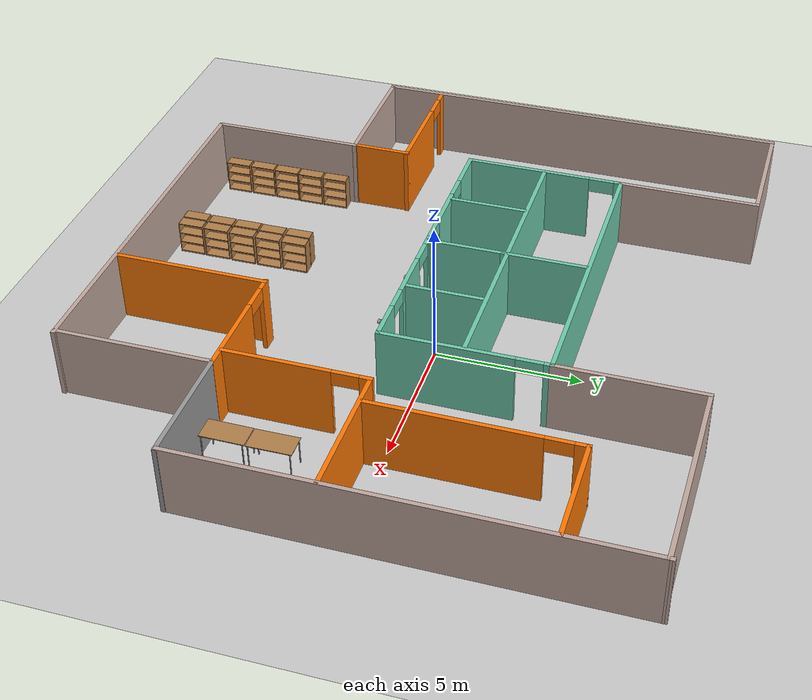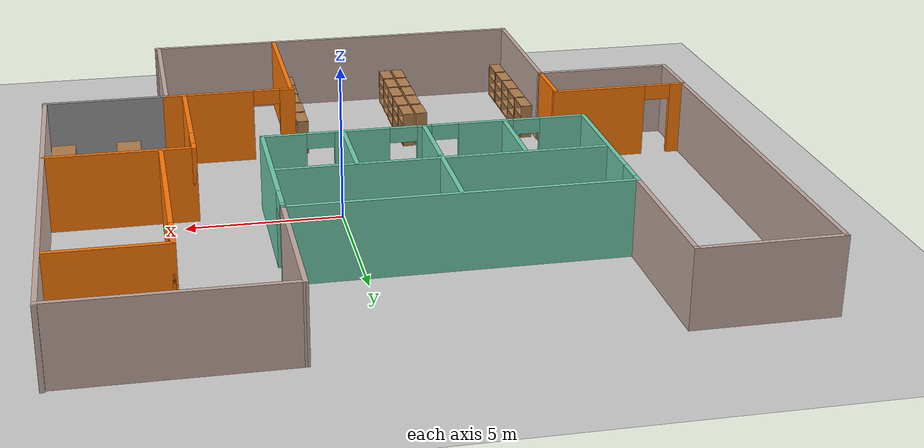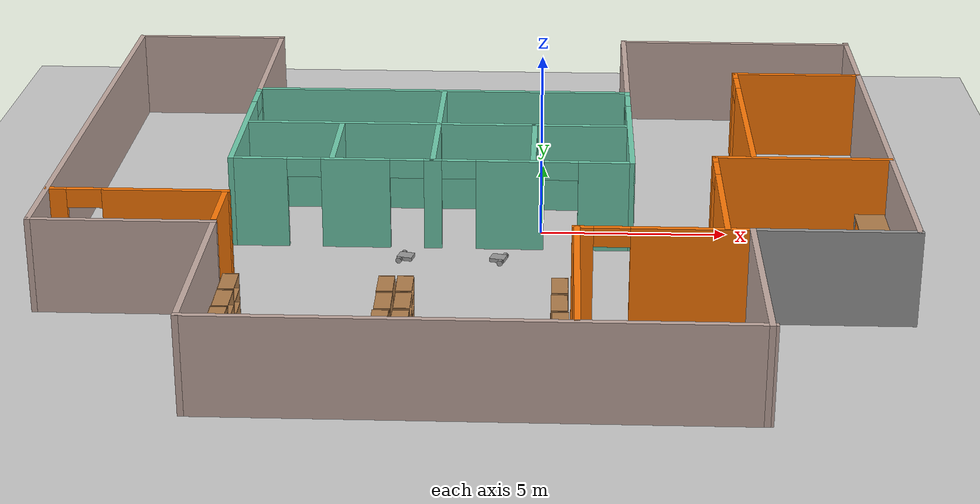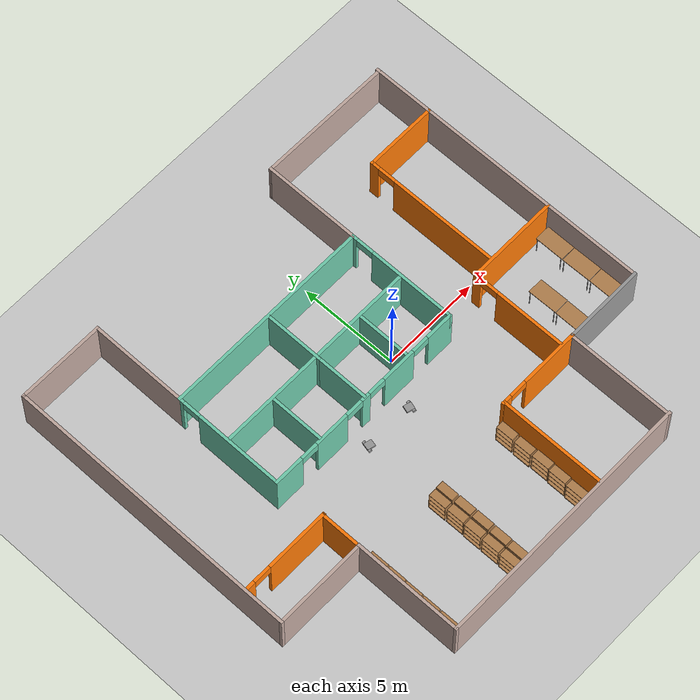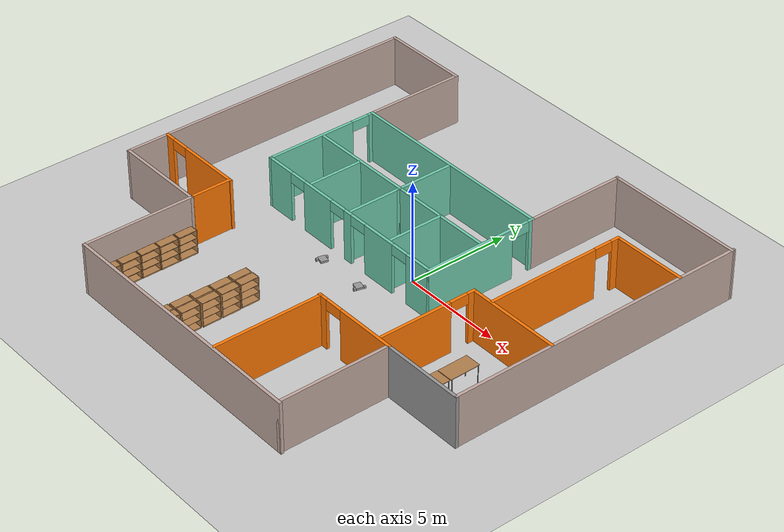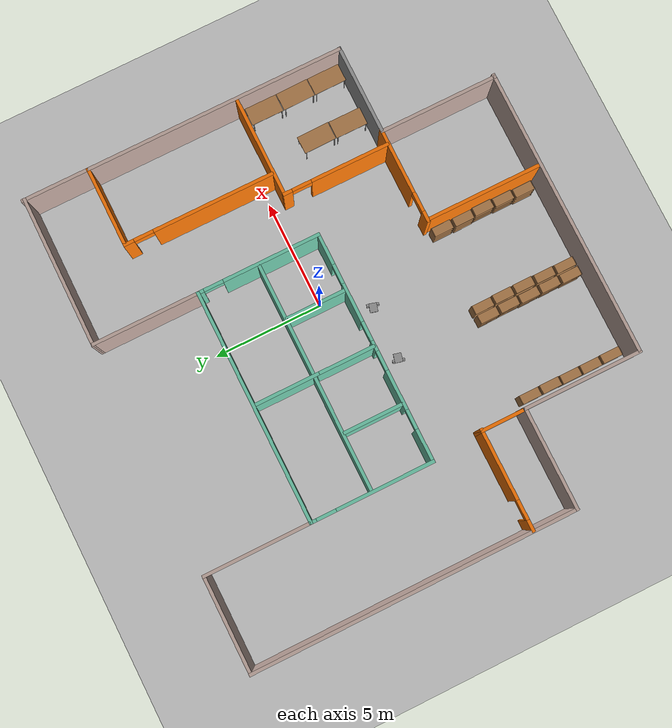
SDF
<sdf version="1.6">
 <world name="default">
  <plugin name="welcome" filename="libwelcome.so"/>
  <light name="sun" type="directional">
   <pose>0 0 10 0 -0 0</pose>
   <diffuse>0.8 0.8 0.8 1</diffuse>
   <specular>0.2 0.2 0.2 1</specular>
   <attenuation>
    <range>1000</range>
    <constant>0.9</constant>
    <linear>0.01</linear>
    <quadratic>0.001</quadratic>
   </attenuation>
   <direction>-0.5 0.1 -0.9</direction>
  </light>
  <model name="ground_plane">
   <static>1</static>
   <link name="link">
    <collision name="collision">
     <geometry><plane><normal>0 0 1</normal><size>100 100</size></plane></geometry>
     <surface>
      <contact><collide_bitmask>65535</collide_bitmask></contact>
      <friction><ode><mu>100</mu><mu2>50</mu2></ode></friction>
     </surface>
    </collision>
    <visual name="visual">
     <cast_shadows>0</cast_shadows>
     <geometry><plane><normal>0 0 1</normal><size>100 100</size></plane></geometry>
     <material>
      <script><uri>file://media/materials/scripts/gazebo.material</uri><name>Gazebo/Grey</name></script>
     </material>
    </visual>
   </link>
  </model>
  <gravity>0 0 -9.8</gravity>
  <magnetic_field>6e-06 2.3e-05 -4.2e-05</magnetic_field>
  <atmosphere type="adiabatic"/>
  <physics name="default_physics" default="0" type="ode">
   <max_step_size>0.001</max_step_size>
   <real_time_factor>1</real_time_factor>
   <real_time_update_rate>1000</real_time_update_rate>
  </physics>
  <scene><ambient>0.4 0.4 0.4 1</ambient><background>0.7 0.7 0.7 1</background><shadows>1</shadows></scene>
  <spherical_coordinates>
   <surface_model>EARTH_WGS84</surface_model>
   <latitude_deg>0</latitude_deg>
   <longitude_deg>0</longitude_deg>
   <elevation>0</elevation>
   <heading_deg>0</heading_deg>
  </spherical_coordinates>
  <model name="Building">
   <pose>-1.6637 -0.76117 0 0 -0 0</pose>
   <link name="Wall_35">
    <collision name="Wall_35_Collision">
     <geometry><box><size>4.5 0.15 2.5</size></box></geometry>
     <pose>0 0 1.25 0 -0 0</pose>
    </collision>
    <visual name="Wall_35_Visual">
     <pose>0 0 1.25 0 -0 0</pose>
     <geometry><box><size>4.5 0.15 2.5</size></box></geometry>
     <material>
      <script><uri>file://media/materials/scripts/gazebo.material</uri><name>Gazebo/Grey</name></script>
      <ambient>0.760784 0.662745 0.627451 1</ambient>
     </material>
     <meta><layer>0</layer></meta>
    </visual>
    <pose>-8.725 10.0804 0 0 -0 0</pose>
   </link>
   <link name="Wall_36">
    <collision name="Wall_36_Collision">
     <geometry><box><size>5 0.15 2.5</size></box></geometry>
     <pose>0 0 1.25 0 -0 0</pose>
    </collision>
    <visual name="Wall_36_Visual">
     <pose>0 0 1.25 0 -0 0</pose>
     <geometry><box><size>5 0.15 2.5</size></box></geometry>
     <material>
      <script><uri>file://media/materials/scripts/gazebo.material</uri><name>Gazebo/Grey</name></script>
      <ambient>0.760784 0.662745 0.627451 1</ambient>
     </material>
     <meta><layer>0</layer></meta>
    </visual>
    <pose>-6.55 7.65538 0 0 0 -1.5708</pose>
   </link>
   <link name="Wall_37">
    <collision name="Wall_37_Collision">
     <geometry><box><size>10.75 0.15 2.5</size></box></geometry>
     <pose>0 0 1.25 0 -0 0</pose>
    </collision>
    <visual name="Wall_37_Visual">
     <pose>0 0 1.25 0 -0 0</pose>
     <geometry><box><size>10.75 0.15 2.5</size></box></geometry>
     <material>
      <script><uri>file://media/materials/scripts/gazebo.material</uri><name>Gazebo/Grey</name></script>
      <ambient>0.435294 0.796078 0.67451 1</ambient>
     </material>
     <meta><layer>0</layer></meta>
    </visual>
    <pose>-1.25 5.23038 0 0 -0 0</pose>
   </link>
   <link name="Wall_38">
    <collision name="Wall_38_Collision">
     <geometry><box><size>5 0.15 2.5</size></box></geometry>
     <pose>0 0 1.25 0 -0 0</pose>
    </collision>
    <visual name="Wall_38_Visual">
     <pose>0 0 1.25 0 -0 0</pose>
     <geometry><box><size>5 0.15 2.5</size></box></geometry>
     <material>
      <script><uri>file://media/materials/scripts/gazebo.material</uri><name>Gazebo/Grey</name></script>
      <ambient>0.760784 0.662745 0.627451 1</ambient>
     </material>
     <meta><layer>0</layer></meta>
    </visual>
    <pose>4.05 7.65538 0 0 -0 1.5708</pose>
   </link>
   <link name="Wall_39">
    <collision name="Wall_39_Collision">
     <geometry><box><size>6.98446 0.15 2.5</size></box></geometry>
     <pose>0 0 1.25 0 -0 0</pose>
    </collision>
    <visual name="Wall_39_Visual">
     <pose>0 0 1.25 0 -0 0</pose>
     <geometry><box><size>6.98446 0.15 2.5</size></box></geometry>
     <material>
      <script><uri>file://media/materials/scripts/gazebo.material</uri><name>Gazebo/Grey</name></script>
      <ambient>0.760784 0.662745 0.627451 1</ambient>
     </material>
     <meta><layer>0</layer></meta>
    </visual>
    <pose>7.46718 10.0598 0 0 0 -0.006031</pose>
   </link>
   <link name="Wall_40">
    <collision name="Wall_40_Collision">
     <geometry><box><size>15 0.15 2.5</size></box></geometry>
     <pose>0 0 1.25 0 -0 0</pose>
    </collision>
    <visual name="Wall_40_Visual">
     <pose>0 0 1.25 0 -0 0</pose>
     <geometry><box><size>15 0.15 2.5</size></box></geometry>
     <material>
      <script><uri>file://media/materials/scripts/gazebo.material</uri><name>Gazebo/Grey</name></script>
      <ambient>0.760784 0.662745 0.627451 1</ambient>
     </material>
     <meta><layer>0</layer></meta>
    </visual>
    <pose>10.8843 2.69462 0 0 0 -1.5708</pose>
   </link>
   <link name="Wall_42">
    <collision name="Wall_42_Collision">
     <geometry><box><size>5.5 0.15 2.5</size></box></geometry>
     <pose>0 0 1.25 0 -0 0</pose>
    </collision>
    <visual name="Wall_42_Visual">
     <pose>0 0 1.25 0 -0 0</pose>
     <geometry><box><size>5.5 0.15 2.5</size></box></geometry>
     <material>
      <script><uri>file://media/materials/scripts/gazebo.material</uri><name>Gazebo/Grey</name></script>
      <ambient>0.760784 0.662745 0.627451 1</ambient>
     </material>
     <meta><layer>0</layer></meta>
    </visual>
    <pose>6.84725 -7.44462 0 0 0 -1.5708</pose>
   </link>
   <link name="Wall_43">
    <collision name="Wall_43_Collision">
     <geometry><box><size>13.368 0.15 2.5</size></box></geometry>
     <pose>0 0 1.25 0 -0 0</pose>
    </collision>
    <visual name="Wall_43_Visual">
     <pose>0 0 1.25 0 -0 0</pose>
     <geometry><box><size>13.368 0.15 2.5</size></box></geometry>
     <material>
      <script><uri>file://media/materials/scripts/gazebo.material</uri><name>Gazebo/Grey</name></script>
      <ambient>0.760784 0.662745 0.627451 1</ambient>
     </material>
     <meta><layer>0</layer></meta>
    </visual>
    <pose>0.309006 -10.1196 0 0 -0 3.14159</pose>
   </link>
   <link name="Wall_44">
    <collision name="Wall_44_Collision">
     <geometry><box><size>5.5 0.15 2.5</size></box></geometry>
     <pose>0 0 1.25 0 -0 0</pose>
    </collision>
    <visual name="Wall_44_Visual">
     <pose>0 0 1.25 0 -0 0</pose>
     <geometry><box><size>5.5 0.15 2.5</size></box></geometry>
     <material>
      <script><uri>file://media/materials/scripts/gazebo.material</uri><name>Gazebo/Grey</name></script>
      <ambient>0.760784 0.662745 0.627451 1</ambient>
     </material>
     <meta><layer>0</layer></meta>
    </visual>
    <pose>-6.3 -7.44462 0 0 -0 1.5708</pose>
   </link>
   <link name="Wall_45">
    <collision name="Wall_45_Collision">
     <geometry><box><size>4.75 0.15 2.5</size></box></geometry>
     <pose>0 0 1.25 0 -0 0</pose>
    </collision>
    <visual name="Wall_45_Visual">
     <pose>0 0 1.25 0 -0 0</pose>
     <geometry><box><size>4.75 0.15 2.5</size></box></geometry>
     <material>
      <script><uri>file://media/materials/scripts/gazebo.material</uri><name>Gazebo/Grey</name></script>
      <ambient>0.760784 0.662745 0.627451 1</ambient>
     </material>
     <meta><layer>0</layer></meta>
    </visual>
    <pose>-8.6 -4.76962 0 0 -0 3.14159</pose>
   </link>
   <link name="Wall_46">
    <collision name="Wall_46_Collision">
     <geometry><box><size>15 0.15 2.5</size></box></geometry>
     <pose>0 0 1.25 0 -0 0</pose>
    </collision>
    <visual name="Wall_46_Visual">
     <pose>0 0 1.25 0 -0 0</pose>
     <geometry><box><size>15 0.15 2.5</size></box></geometry>
     <material>
      <script><uri>file://media/materials/scripts/gazebo.material</uri><name>Gazebo/Grey</name></script>
      <ambient>0.760784 0.662745 0.627451 1</ambient>
     </material>
     <meta><layer>0</layer></meta>
    </visual>
    <pose>-10.9 2.65538 0 0 -0 1.5708</pose>
   </link>
   <link name="Wall_48">
    <pose>-6.55 2.43038 0 0 0 -1.5708</pose>
    <visual name="Wall_48_Visual_0">
     <pose>-2.70872 0 1.25 0 -0 0</pose>
     <geometry><box><size>0.332563 0.15 2.5</size></box></geometry>
     <material>
      <script><uri>file://media/materials/scripts/gazebo.material</uri><name>Gazebo/Grey</name></script>
      <ambient>0.435294 0.796078 0.67451 1</ambient>
     </material>
     <meta><layer>0</layer></meta>
    </visual>
    <collision name="Wall_48_Collision_0">
     <geometry><box><size>0.332563 0.15 2.5</size></box></geometry>
     <pose>-2.70872 0 1.25 0 -0 0</pose>
    </collision>
    <visual name="Wall_48_Visual_1">
     <pose>0.616281 0 1.25 0 -0 0</pose>
     <geometry><box><size>4.51744 0.15 2.5</size></box></geometry>
     <material>
      <script><uri>file://media/materials/scripts/gazebo.material</uri><name>Gazebo/Grey</name></script>
      <ambient>0.435294 0.796078 0.67451 1</ambient>
     </material>
     <meta><layer>0</layer></meta>
    </visual>
    <collision name="Wall_48_Collision_1">
     <geometry><box><size>4.51744 0.15 2.5</size></box></geometry>
     <pose>0.616281 0 1.25 0 -0 0</pose>
    </collision>
    <visual name="Wall_48_Visual_2">
     <pose>-2.09244 0 2.25 0 -0 0</pose>
     <geometry><box><size>0.9 0.15 0.5</size></box></geometry>
     <material>
      <script><uri>file://media/materials/scripts/gazebo.material</uri><name>Gazebo/Grey</name></script>
      <ambient>0.435294 0.796078 0.67451 1</ambient>
     </material>
     <meta><layer>0</layer></meta>
    </visual>
    <collision name="Wall_48_Collision_2">
     <geometry><box><size>0.9 0.15 0.5</size></box></geometry>
     <pose>-2.09244 0 2.25 0 -0 0</pose>
    </collision>
   </link>
   <link name="Wall_49">
    <pose>-1.25 -0.36962 0 0 -0 0</pose>
    <visual name="Wall_49_Visual_0">
     <pose>-4.59292 0 1.25 0 -0 0</pose>
     <geometry><box><size>1.56416 0.15 2.5</size></box></geometry>
     <material>
      <script><uri>file://media/materials/scripts/gazebo.material</uri><name>Gazebo/Grey</name></script>
      <ambient>0.435294 0.796078 0.67451 1</ambient>
     </material>
     <meta><layer>0</layer></meta>
    </visual>
    <collision name="Wall_49_Collision_0">
     <geometry><box><size>1.56416 0.15 2.5</size></box></geometry>
     <pose>-4.59292 0 1.25 0 -0 0</pose>
    </collision>
    <visual name="Wall_49_Visual_1">
     <pose>-2.00006 0 1.25 0 -0 0</pose>
     <geometry><box><size>1.82155 0.15 2.5</size></box></geometry>
     <material>
      <script><uri>file://media/materials/scripts/gazebo.material</uri><name>Gazebo/Grey</name></script>
      <ambient>0.435294 0.796078 0.67451 1</ambient>
     </material>
     <meta><layer>0</layer></meta>
    </visual>
    <collision name="Wall_49_Collision_1">
     <geometry><box><size>1.82155 0.15 2.5</size></box></geometry>
     <pose>-2.00006 0 1.25 0 -0 0</pose>
    </collision>
    <visual name="Wall_49_Visual_2">
     <pose>0.046812 0 1.25 0 -0 0</pose>
     <geometry><box><size>0.472208 0.15 2.5</size></box></geometry>
     <material>
      <script><uri>file://media/materials/scripts/gazebo.material</uri><name>Gazebo/Grey</name></script>
      <ambient>0.435294 0.796078 0.67451 1</ambient>
     </material>
     <meta><layer>0</layer></meta>
    </visual>
    <collision name="Wall_49_Collision_2">
     <geometry><box><size>0.472208 0.15 2.5</size></box></geometry>
     <pose>0.046812 0 1.25 0 -0 0</pose>
    </collision>
    <visual name="Wall_49_Visual_3">
     <pose>2.08225 0 1.25 0 -0 0</pose>
     <geometry><box><size>1.79868 0.15 2.5</size></box></geometry>
     <material>
      <script><uri>file://media/materials/scripts/gazebo.material</uri><name>Gazebo/Grey</name></script>
      <ambient>0.435294 0.796078 0.67451 1</ambient>
     </material>
     <meta><layer>0</layer></meta>
    </visual>
    <collision name="Wall_49_Collision_3">
     <geometry><box><size>1.79868 0.15 2.5</size></box></geometry>
     <pose>2.08225 0 1.25 0 -0 0</pose>
    </collision>
    <visual name="Wall_49_Visual_4">
     <pose>4.6283 0 1.25 0 -0 0</pose>
     <geometry><box><size>1.49341 0.15 2.5</size></box></geometry>
     <material>
      <script><uri>file://media/materials/scripts/gazebo.material</uri><name>Gazebo/Grey</name></script>
      <ambient>0.435294 0.796078 0.67451 1</ambient>
     </material>
     <meta><layer>0</layer></meta>
    </visual>
    <collision name="Wall_49_Collision_4">
     <geometry><box><size>1.49341 0.15 2.5</size></box></geometry>
     <pose>4.6283 0 1.25 0 -0 0</pose>
    </collision>
    <visual name="Wall_49_Visual_5">
     <pose>-3.36084 0 2.25 0 -0 0</pose>
     <geometry><box><size>0.9 0.15 0.5</size></box></geometry>
     <material>
      <script><uri>file://media/materials/scripts/gazebo.material</uri><name>Gazebo/Grey</name></script>
      <ambient>0.435294 0.796078 0.67451 1</ambient>
     </material>
     <meta><layer>0</layer></meta>
    </visual>
    <collision name="Wall_49_Collision_5">
     <geometry><box><size>0.9 0.15 0.5</size></box></geometry>
     <pose>-3.36084 0 2.25 0 -0 0</pose>
    </collision>
    <visual name="Wall_49_Visual_6">
     <pose>-0.639292 0 2.25 0 -0 0</pose>
     <geometry><box><size>0.9 0.15 0.5</size></box></geometry>
     <material>
      <script><uri>file://media/materials/scripts/gazebo.material</uri><name>Gazebo/Grey</name></script>
      <ambient>0.435294 0.796078 0.67451 1</ambient>
     </material>
     <meta><layer>0</layer></meta>
    </visual>
    <collision name="Wall_49_Collision_6">
     <geometry><box><size>0.9 0.15 0.5</size></box></geometry>
     <pose>-0.639292 0 2.25 0 -0 0</pose>
    </collision>
    <visual name="Wall_49_Visual_7">
     <pose>0.732916 0 2.25 0 -0 0</pose>
     <geometry><box><size>0.9 0.15 0.5</size></box></geometry>
     <material>
      <script><uri>file://media/materials/scripts/gazebo.material</uri><name>Gazebo/Grey</name></script>
      <ambient>0.435294 0.796078 0.67451 1</ambient>
     </material>
     <meta><layer>0</layer></meta>
    </visual>
    <collision name="Wall_49_Collision_7">
     <geometry><box><size>0.9 0.15 0.5</size></box></geometry>
     <pose>0.732916 0 2.25 0 -0 0</pose>
    </collision>
    <visual name="Wall_49_Visual_8">
     <pose>3.43159 0 2.25 0 -0 0</pose>
     <geometry><box><size>0.9 0.15 0.5</size></box></geometry>
     <material>
      <script><uri>file://media/materials/scripts/gazebo.material</uri><name>Gazebo/Grey</name></script>
      <ambient>0.435294 0.796078 0.67451 1</ambient>
     </material>
     <meta><layer>0</layer></meta>
    </visual>
    <collision name="Wall_49_Collision_8">
     <geometry><box><size>0.9 0.15 0.5</size></box></geometry>
     <pose>3.43159 0 2.25 0 -0 0</pose>
    </collision>
   </link>
   <link name="Wall_50">
    <pose>4.05 2.43038 0 0 -0 1.5708</pose>
    <visual name="Wall_50_Visual_0">
     <pose>-0.616281 0 1.25 0 -0 0</pose>
     <geometry><box><size>4.51744 0.15 2.5</size></box></geometry>
     <material>
      <script><uri>file://media/materials/scripts/gazebo.material</uri><name>Gazebo/Grey</name></script>
      <ambient>0.435294 0.796078 0.67451 1</ambient>
     </material>
     <meta><layer>0</layer></meta>
    </visual>
    <collision name="Wall_50_Collision_0">
     <geometry><box><size>4.51744 0.15 2.5</size></box></geometry>
     <pose>-0.616281 0 1.25 0 -0 0</pose>
    </collision>
    <visual name="Wall_50_Visual_1">
     <pose>2.70872 0 1.25 0 -0 0</pose>
     <geometry><box><size>0.332563 0.15 2.5</size></box></geometry>
     <material>
      <script><uri>file://media/materials/scripts/gazebo.material</uri><name>Gazebo/Grey</name></script>
      <ambient>0.435294 0.796078 0.67451 1</ambient>
     </material>
     <meta><layer>0</layer></meta>
    </visual>
    <collision name="Wall_50_Collision_1">
     <geometry><box><size>0.332563 0.15 2.5</size></box></geometry>
     <pose>2.70872 0 1.25 0 -0 0</pose>
    </collision>
    <visual name="Wall_50_Visual_2">
     <pose>2.09244 0 2.25 0 -0 0</pose>
     <geometry><box><size>0.9 0.15 0.5</size></box></geometry>
     <material>
      <script><uri>file://media/materials/scripts/gazebo.material</uri><name>Gazebo/Grey</name></script>
      <ambient>0.435294 0.796078 0.67451 1</ambient>
     </material>
     <meta><layer>0</layer></meta>
    </visual>
    <collision name="Wall_50_Collision_2">
     <geometry><box><size>0.9 0.15 0.5</size></box></geometry>
     <pose>2.09244 0 2.25 0 -0 0</pose>
    </collision>
   </link>
   <link name="Wall_52">
    <collision name="Wall_52_Collision">
     <geometry><box><size>10.5 0.15 2.5</size></box></geometry>
     <pose>0 0 1.25 0 -0 0</pose>
    </collision>
    <visual name="Wall_52_Visual">
     <pose>0 0 1.25 0 -0 0</pose>
     <geometry><box><size>10.5 0.15 2.5</size></box></geometry>
     <material>
      <script><uri>file://media/materials/scripts/gazebo.material</uri><name>Gazebo/Grey</name></script>
      <ambient>0.435294 0.796078 0.67451 1</ambient>
     </material>
     <meta><layer>0</layer></meta>
    </visual>
    <pose>-1.24961 2.43154 0 0 -0 0</pose>
   </link>
   <link name="Wall_56">
    <collision name="Wall_56_Collision">
     <geometry><box><size>2.75 0.15 2.5</size></box></geometry>
     <pose>0 0 1.25 0 -0 0</pose>
    </collision>
    <visual name="Wall_56_Visual">
     <pose>0 0 1.25 0 -0 0</pose>
     <geometry><box><size>2.75 0.15 2.5</size></box></geometry>
     <material>
      <script><uri>file://media/materials/scripts/gazebo.material</uri><name>Gazebo/Grey</name></script>
      <ambient>0.435294 0.796078 0.67451 1</ambient>
     </material>
     <meta><layer>0</layer></meta>
    </visual>
    <pose>-1.20548 0.975756 0 0 0 -1.5708</pose>
   </link>
   <link name="Wall_59">
    <collision name="Wall_59_Collision">
     <geometry><box><size>2.75 0.15 2.5</size></box></geometry>
     <pose>0 0 1.25 0 -0 0</pose>
    </collision>
    <visual name="Wall_59_Visual">
     <pose>0 0 1.25 0 -0 0</pose>
     <geometry><box><size>2.75 0.15 2.5</size></box></geometry>
     <material>
      <script><uri>file://media/materials/scripts/gazebo.material</uri><name>Gazebo/Grey</name></script>
      <ambient>0.435294 0.796078 0.67451 1</ambient>
     </material>
     <meta><layer>0</layer></meta>
    </visual>
    <pose>-3.87235 1.03442 0 0 0 -1.5708</pose>
   </link>
   <link name="Wall_61">
    <collision name="Wall_61_Collision">
     <geometry><box><size>2.75 0.15 2.5</size></box></geometry>
     <pose>0 0 1.25 0 -0 0</pose>
    </collision>
    <visual name="Wall_61_Visual">
     <pose>0 0 1.25 0 -0 0</pose>
     <geometry><box><size>2.75 0.15 2.5</size></box></geometry>
     <material>
      <script><uri>file://media/materials/scripts/gazebo.material</uri><name>Gazebo/Grey</name></script>
      <ambient>0.435294 0.796078 0.67451 1</ambient>
     </material>
     <meta><layer>0</layer></meta>
    </visual>
    <pose>1.44292 1.07244 0 0 0 -1.5708</pose>
   </link>
   <link name="Wall_63">
    <collision name="Wall_63_Collision">
     <geometry><box><size>3 0.15 2.5</size></box></geometry>
     <pose>0 0 1.25 0 -0 0</pose>
    </collision>
    <visual name="Wall_63_Visual">
     <pose>0 0 1.25 0 -0 0</pose>
     <geometry><box><size>3 0.15 2.5</size></box></geometry>
     <material>
      <script><uri>file://media/materials/scripts/gazebo.material</uri><name>Gazebo/Grey</name></script>
      <ambient>0.435294 0.796078 0.67451 1</ambient>
     </material>
     <meta><layer>0</layer></meta>
    </visual>
    <pose>-1.20548 3.70076 0 0 -0 1.5708</pose>
   </link>
   <link name="Wall_65">
    <collision name="Wall_65_Collision">
     <geometry><box><size>4.13199 0.15 2.5</size></box></geometry>
     <pose>0 0 1.25 0 -0 0</pose>
    </collision>
    <visual name="Wall_65_Visual">
     <pose>0 0 1.25 0 -0 0</pose>
     <geometry><box><size>4.13199 0.15 2.5</size></box></geometry>
     <material>
      <script><uri>file://media/materials/scripts/gazebo.material</uri><name>Gazebo/Grey</name></script>
      <ambient>1 1 1 1</ambient>
     </material>
     <meta><layer>0</layer></meta>
    </visual>
    <pose>8.90901 -4.76962 0 0 -0 0</pose>
   </link>
   <link name="Wall_67">
    <collision name="Wall_67_Collision">
     <geometry><box><size>5.40695 0.15 2.5</size></box></geometry>
     <pose>0 0 1.25 0 -0 0</pose>
    </collision>
    <visual name="Wall_67_Visual">
     <pose>0 0 1.25 0 -0 0</pose>
     <geometry><box><size>5.40695 0.15 2.5</size></box></geometry>
     <material>
      <script><uri>file://media/materials/scripts/gazebo.material</uri><name>Gazebo/Grey</name></script>
      <ambient>0.996078 0.47451 0.0196078 1</ambient>
     </material>
     <meta><layer>0</layer></meta>
    </visual>
    <pose>2.58189 -7.39438 0 0 -0 1.5708</pose>
   </link>
   <link name="Wall_68">
    <pose>4.71037 -4.7659 0 0 -0 0</pose>
    <visual name="Wall_68_Visual_0">
     <pose>-1.98659 0 1.25 0 -0 0</pose>
     <geometry><box><size>0.526825 0.15 2.5</size></box></geometry>
     <material>
      <script><uri>file://media/materials/scripts/gazebo.material</uri><name>Gazebo/Grey</name></script>
      <ambient>0.996078 0.47451 0.0196078 1</ambient>
     </material>
     <meta><layer>0</layer></meta>
    </visual>
    <collision name="Wall_68_Collision_0">
     <geometry><box><size>0.526825 0.15 2.5</size></box></geometry>
     <pose>-1.98659 0 1.25 0 -0 0</pose>
    </collision>
    <visual name="Wall_68_Visual_1">
     <pose>0.713412 0 1.25 0 -0 0</pose>
     <geometry><box><size>3.07317 0.15 2.5</size></box></geometry>
     <material>
      <script><uri>file://media/materials/scripts/gazebo.material</uri><name>Gazebo/Grey</name></script>
      <ambient>0.996078 0.47451 0.0196078 1</ambient>
     </material>
     <meta><layer>0</layer></meta>
    </visual>
    <collision name="Wall_68_Collision_1">
     <geometry><box><size>3.07317 0.15 2.5</size></box></geometry>
     <pose>0.713412 0 1.25 0 -0 0</pose>
    </collision>
    <visual name="Wall_68_Visual_2">
     <pose>-1.27317 0 2.25 0 -0 0</pose>
     <geometry><box><size>0.9 0.15 0.5</size></box></geometry>
     <material>
      <script><uri>file://media/materials/scripts/gazebo.material</uri><name>Gazebo/Grey</name></script>
      <ambient>0.996078 0.47451 0.0196078 1</ambient>
     </material>
     <meta><layer>0</layer></meta>
    </visual>
    <collision name="Wall_68_Collision_2">
     <geometry><box><size>0.9 0.15 0.5</size></box></geometry>
     <pose>-1.27317 0 2.25 0 -0 0</pose>
    </collision>
   </link>
   <link name="Wall_70">
    <pose>6.24178 -2.28341 0 0 -0 1.5708</pose>
    <visual name="Wall_70_Visual_0">
     <pose>-0.668588 0 1.25 0 -0 0</pose>
     <geometry><box><size>3.66283 0.15 2.5</size></box></geometry>
     <material>
      <script><uri>file://media/materials/scripts/gazebo.material</uri><name>Gazebo/Grey</name></script>
      <ambient>0.996078 0.47451 0.0196078 1</ambient>
     </material>
     <meta><layer>0</layer></meta>
    </visual>
    <collision name="Wall_70_Collision_0">
     <geometry><box><size>3.66283 0.15 2.5</size></box></geometry>
     <pose>-0.668588 0 1.25 0 -0 0</pose>
    </collision>
    <visual name="Wall_70_Visual_1">
     <pose>2.28141 0 1.25 0 -0 0</pose>
     <geometry><box><size>0.437175 0.15 2.5</size></box></geometry>
     <material>
      <script><uri>file://media/materials/scripts/gazebo.material</uri><name>Gazebo/Grey</name></script>
      <ambient>0.996078 0.47451 0.0196078 1</ambient>
     </material>
     <meta><layer>0</layer></meta>
    </visual>
    <collision name="Wall_70_Collision_1">
     <geometry><box><size>0.437175 0.15 2.5</size></box></geometry>
     <pose>2.28141 0 1.25 0 -0 0</pose>
    </collision>
    <visual name="Wall_70_Visual_2">
     <pose>1.61282 0 2.25 0 -0 0</pose>
     <geometry><box><size>0.9 0.15 0.5</size></box></geometry>
     <material>
      <script><uri>file://media/materials/scripts/gazebo.material</uri><name>Gazebo/Grey</name></script>
      <ambient>0.996078 0.47451 0.0196078 1</ambient>
     </material>
     <meta><layer>0</layer></meta>
    </visual>
    <collision name="Wall_70_Collision_2">
     <geometry><box><size>0.9 0.15 0.5</size></box></geometry>
     <pose>1.61282 0 2.25 0 -0 0</pose>
    </collision>
   </link>
   <link name="Wall_71">
    <collision name="Wall_71_Collision">
     <geometry><box><size>4.75 0.15 2.5</size></box></geometry>
     <pose>0 0 1.25 0 -0 0</pose>
    </collision>
    <visual name="Wall_71_Visual">
     <pose>0 0 1.25 0 -0 0</pose>
     <geometry><box><size>4.75 0.15 2.5</size></box></geometry>
     <material>
      <script><uri>file://media/materials/scripts/gazebo.material</uri><name>Gazebo/Grey</name></script>
      <ambient>0.996078 0.47451 0.0196078 1</ambient>
     </material>
     <meta><layer>0</layer></meta>
    </visual>
    <pose>8.54178 0.141587 0 0 -0 0</pose>
   </link>
   <link name="Wall_73">
    <pose>7.26632 3.65979 0 0 -0 1.5708</pose>
    <visual name="Wall_73_Visual_0">
     <pose>-0.697419 0 1.25 0 -0 0</pose>
     <geometry><box><size>5.60516 0.15 2.5</size></box></geometry>
     <material>
      <script><uri>file://media/materials/scripts/gazebo.material</uri><name>Gazebo/Grey</name></script>
      <ambient>0.996078 0.47451 0.0196078 1</ambient>
     </material>
     <meta><layer>0</layer></meta>
    </visual>
    <collision name="Wall_73_Collision_0">
     <geometry><box><size>5.60516 0.15 2.5</size></box></geometry>
     <pose>-0.697419 0 1.25 0 -0 0</pose>
    </collision>
    <visual name="Wall_73_Visual_1">
     <pose>3.25258 0 1.25 0 -0 0</pose>
     <geometry><box><size>0.494839 0.15 2.5</size></box></geometry>
     <material>
      <script><uri>file://media/materials/scripts/gazebo.material</uri><name>Gazebo/Grey</name></script>
      <ambient>0.996078 0.47451 0.0196078 1</ambient>
     </material>
     <meta><layer>0</layer></meta>
    </visual>
    <collision name="Wall_73_Collision_1">
     <geometry><box><size>0.494839 0.15 2.5</size></box></geometry>
     <pose>3.25258 0 1.25 0 -0 0</pose>
    </collision>
    <visual name="Wall_73_Visual_2">
     <pose>2.55516 0 2.25 0 -0 0</pose>
     <geometry><box><size>0.9 0.15 0.5</size></box></geometry>
     <material>
      <script><uri>file://media/materials/scripts/gazebo.material</uri><name>Gazebo/Grey</name></script>
      <ambient>0.996078 0.47451 0.0196078 1</ambient>
     </material>
     <meta><layer>0</layer></meta>
    </visual>
    <collision name="Wall_73_Collision_2">
     <geometry><box><size>0.9 0.15 0.5</size></box></geometry>
     <pose>2.55516 0 2.25 0 -0 0</pose>
    </collision>
   </link>
   <link name="Wall_74">
    <collision name="Wall_74_Collision">
     <geometry><box><size>3.75 0.15 2.5</size></box></geometry>
     <pose>0 0 1.25 0 -0 0</pose>
    </collision>
    <visual name="Wall_74_Visual">
     <pose>0 0 1.25 0 -0 0</pose>
     <geometry><box><size>3.75 0.15 2.5</size></box></geometry>
     <material>
      <script><uri>file://media/materials/scripts/gazebo.material</uri><name>Gazebo/Grey</name></script>
      <ambient>0.996078 0.47451 0.0196078 1</ambient>
     </material>
     <meta><layer>0</layer></meta>
    </visual>
    <pose>9.06632 7.08479 0 0 -0 0</pose>
   </link>
   <link name="Wall_78">
    <pose>-8.57396 -2.7529 0 0 -0 0</pose>
    <visual name="Wall_78_Visual_0">
     <pose>-2.09 0 1.25 0 -0 0</pose>
     <geometry><box><size>0.555478 0.15 2.5</size></box></geometry>
     <material>
      <script><uri>file://media/materials/scripts/gazebo.material</uri><name>Gazebo/Grey</name></script>
      <ambient>0.996078 0.47451 0.0196078 1</ambient>
     </material>
     <meta><layer>0</layer></meta>
    </visual>
    <collision name="Wall_78_Collision_0">
     <geometry><box><size>0.555478 0.15 2.5</size></box></geometry>
     <pose>-2.09 0 1.25 0 -0 0</pose>
    </collision>
    <visual name="Wall_78_Visual_1">
     <pose>0.727739 0 1.25 0 -0 0</pose>
     <geometry><box><size>3.27999 0.15 2.5</size></box></geometry>
     <material>
      <script><uri>file://media/materials/scripts/gazebo.material</uri><name>Gazebo/Grey</name></script>
      <ambient>0.996078 0.47451 0.0196078 1</ambient>
     </material>
     <meta><layer>0</layer></meta>
    </visual>
    <collision name="Wall_78_Collision_1">
     <geometry><box><size>3.27999 0.15 2.5</size></box></geometry>
     <pose>0.727739 0 1.25 0 -0 0</pose>
    </collision>
    <visual name="Wall_78_Visual_2">
     <pose>-1.36226 0 2.25 0 -0 0</pose>
     <geometry><box><size>0.9 0.15 0.5</size></box></geometry>
     <material>
      <script><uri>file://media/materials/scripts/gazebo.material</uri><name>Gazebo/Grey</name></script>
      <ambient>0.996078 0.47451 0.0196078 1</ambient>
     </material>
     <meta><layer>0</layer></meta>
    </visual>
    <collision name="Wall_78_Collision_2">
     <geometry><box><size>0.9 0.15 0.5</size></box></geometry>
     <pose>-1.36226 0 2.25 0 -0 0</pose>
    </collision>
   </link>
   <link name="Wall_80">
    <collision name="Wall_80_Collision">
     <geometry><box><size>2 0.15 2.5</size></box></geometry>
     <pose>0 0 1.25 0 -0 0</pose>
    </collision>
    <visual name="Wall_80_Visual">
     <pose>0 0 1.25 0 -0 0</pose>
     <geometry><box><size>2 0.15 2.5</size></box></geometry>
     <material>
      <script><uri>file://media/materials/scripts/gazebo.material</uri><name>Gazebo/Grey</name></script>
      <ambient>0.996078 0.47451 0.0196078 1</ambient>
     </material>
     <meta><layer>0</layer></meta>
    </visual>
    <pose>-6.32169 -3.6779 0 0 0 -1.5708</pose>
   </link>
   <static>1</static>
  </model>
  <model name="CasterWheelRobot">
   <link name="link_2">
    <pose>0.03 0 0.025 0 -0 0</pose>
    <inertial>
     <mass>0.0155432</mass>
     <inertia>
      <ixx>0.0001924</ixx>
      <ixy>0</ixy>
      <ixz>0</ixz>
      <iyy>0.0002189</iyy>
      <iyz>0</iyz>
      <izz>0.00038243</izz>
     </inertia>
    </inertial>
    <visual name="visual">
     <geometry><box><size>0.4 0.35 0.1</size></box></geometry>
     <material>
      <lighting>1</lighting>
      <script><uri>file://media/materials/scripts/gazebo.material</uri><name>Gazebo/Grey</name></script>
      <shader type="pixel"><normal_map>__default__</normal_map></shader>
      <ambient>0.3 0.3 0.3 1</ambient>
      <diffuse>0.7 0.7 0.7 1</diffuse>
      <specular>0.01 0.01 0.01 1</specular>
      <emissive>0 0 0 1</emissive>
     </material>
    </visual>
    <collision name="collision">
     <geometry><box><size>0.4 0.35 0.1</size></box></geometry>
     <surface>
      <friction>
       <ode><mu>1</mu><mu2>1</mu2><fdir1>0 0 0</fdir1><slip1>0</slip1><slip2>0</slip2></ode>
       <torsional>
        <coefficient>1</coefficient>
        <patch_radius>0</patch_radius>
        <surface_radius>0</surface_radius>
        <use_patch_radius>1</use_patch_radius>
        <ode><slip>0</slip></ode>
       </torsional>
      </friction>
      <bounce><restitution_coefficient>0</restitution_coefficient><threshold>1e+06</threshold></bounce>
      <contact>
       <collide_without_contact>0</collide_without_contact>
       <collide_without_contact_bitmask>1</collide_without_contact_bitmask>
       <collide_bitmask>1</collide_bitmask>
       <ode>
        <soft_cfm>0</soft_cfm>
        <soft_erp>0.2</soft_erp>
        <kp>1e+13</kp>
        <kd>1</kd>
        <max_vel>0.01</max_vel>
        <min_depth>0</min_depth>
       </ode>
       <bullet>
        <split_impulse>1</split_impulse>
        <split_impulse_penetration_threshold>-0.01</split_impulse_penetration_threshold>
        <soft_cfm>0</soft_cfm>
        <soft_erp>0.2</soft_erp>
        <kp>1e+13</kp>
        <kd>1</kd>
       </bullet>
      </contact>
     </surface>
    </collision>
   </link>
   <link name="link_3">
    <pose>-0.09 -0.225013 0.005 1.5707 -0 0</pose>
    <inertial>
     <mass>1</mass>
     <inertia><ixx>0.145833</ixx><ixy>0</ixy><ixz>0</ixz><iyy>0.145833</iyy><iyz>0</iyz><izz>0.125</izz></inertia>
    </inertial>
    <visual name="visual">
     <geometry><cylinder><radius>0.08</radius><length>0.1</length></cylinder></geometry>
     <material>
      <lighting>1</lighting>
      <script><uri>file://media/materials/scripts/gazebo.material</uri><name>Gazebo/Grey</name></script>
      <shader type="pixel"><normal_map>__default__</normal_map></shader>
      <ambient>0.3 0.3 0.3 1</ambient>
      <diffuse>0.7 0.7 0.7 1</diffuse>
      <specular>0.01 0.01 0.01 1</specular>
      <emissive>0 0 0 1</emissive>
     </material>
    </visual>
    <collision name="collision">
     <geometry><cylinder><radius>0.08</radius><length>0.1</length></cylinder></geometry>
     <surface>
      <friction>
       <ode><mu>1</mu><mu2>1</mu2><fdir1>0 0 0</fdir1><slip1>0</slip1><slip2>0</slip2></ode>
       <torsional>
        <coefficient>1</coefficient>
        <patch_radius>0</patch_radius>
        <surface_radius>0</surface_radius>
        <use_patch_radius>1</use_patch_radius>
        <ode><slip>0</slip></ode>
       </torsional>
      </friction>
      <bounce><restitution_coefficient>0</restitution_coefficient><threshold>1e+06</threshold></bounce>
      <contact>
       <collide_without_contact>0</collide_without_contact>
       <collide_without_contact_bitmask>1</collide_without_contact_bitmask>
       <collide_bitmask>1</collide_bitmask>
       <ode>
        <soft_cfm>0</soft_cfm>
        <soft_erp>0.2</soft_erp>
        <kp>1e+13</kp>
        <kd>1</kd>
        <max_vel>0.01</max_vel>
        <min_depth>0</min_depth>
       </ode>
       <bullet>
        <split_impulse>1</split_impulse>
        <split_impulse_penetration_threshold>-0.01</split_impulse_penetration_threshold>
        <soft_cfm>0</soft_cfm>
        <soft_erp>0.2</soft_erp>
        <kp>1e+13</kp>
        <kd>1</kd>
       </bullet>
      </contact>
     </surface>
    </collision>
   </link>
   <link name="link_3_clone">
    <pose>-0.09 0.225008 0.005 -1.5707 0 0</pose>
    <inertial>
     <mass>1</mass>
     <inertia><ixx>0.145833</ixx><ixy>0</ixy><ixz>0</ixz><iyy>0.145833</iyy><iyz>0</iyz><izz>0.125</izz></inertia>
    </inertial>
    <visual name="visual">
     <geometry><cylinder><radius>0.08</radius><length>0.1</length></cylinder></geometry>
     <material>
      <lighting>1</lighting>
      <script><uri>file://media/materials/scripts/gazebo.material</uri><name>Gazebo/Grey</name></script>
      <shader type="pixel"><normal_map>__default__</normal_map></shader>
      <ambient>0.3 0.3 0.3 1</ambient>
      <diffuse>0.7 0.7 0.7 1</diffuse>
      <specular>0.01 0.01 0.01 1</specular>
      <emissive>0 0 0 1</emissive>
     </material>
    </visual>
    <collision name="collision">
     <geometry><cylinder><radius>0.08</radius><length>0.1</length></cylinder></geometry>
     <surface>
      <friction>
       <ode><mu>1</mu><mu2>1</mu2><fdir1>0 0 0</fdir1><slip1>0</slip1><slip2>0</slip2></ode>
       <torsional>
        <coefficient>1</coefficient>
        <patch_radius>0</patch_radius>
        <surface_radius>0</surface_radius>
        <use_patch_radius>1</use_patch_radius>
        <ode><slip>0</slip></ode>
       </torsional>
      </friction>
      <bounce><restitution_coefficient>0</restitution_coefficient><threshold>1e+06</threshold></bounce>
      <contact>
       <collide_without_contact>0</collide_without_contact>
       <collide_without_contact_bitmask>1</collide_without_contact_bitmask>
       <collide_bitmask>1</collide_bitmask>
       <ode>
        <soft_cfm>0</soft_cfm>
        <soft_erp>0.2</soft_erp>
        <kp>1e+13</kp>
        <kd>1</kd>
        <max_vel>0.01</max_vel>
        <min_depth>0</min_depth>
       </ode>
       <bullet>
        <split_impulse>1</split_impulse>
        <split_impulse_penetration_threshold>-0.01</split_impulse_penetration_threshold>
        <soft_cfm>0</soft_cfm>
        <soft_erp>0.2</soft_erp>
        <kp>1e+13</kp>
        <kd>1</kd>
       </bullet>
      </contact>
     </surface>
    </collision>
   </link>
   <link name="link_4">
    <pose>0.15 0 -0.035 0 -0 0</pose>
    <inertial>
     <mass>0.00336129</mass>
     <inertia>
      <ixx>7.54e-06</ixx>
      <ixy>0</ixy>
      <ixz>0</ixz>
      <iyy>7.54e-06</iyy>
      <iyz>0</iyz>
      <izz>7.54e-06</izz>
     </inertia>
    </inertial>
    <visual name="visual">
     <geometry><sphere><radius>0.04</radius></sphere></geometry>
     <material>
      <lighting>1</lighting>
      <script><uri>file://media/materials/scripts/gazebo.material</uri><name>Gazebo/Grey</name></script>
      <shader type="pixel"><normal_map>__default__</normal_map></shader>
      <ambient>0.3 0.3 0.3 1</ambient>
      <diffuse>0.7 0.7 0.7 1</diffuse>
      <specular>0.01 0.01 0.01 1</specular>
      <emissive>0 0 0 1</emissive>
     </material>
    </visual>
    <collision name="collision">
     <geometry><sphere><radius>0.04</radius></sphere></geometry>
     <surface>
      <friction>
       <ode><mu>1</mu><mu2>1</mu2><fdir1>0 0 0</fdir1><slip1>0</slip1><slip2>0</slip2></ode>
       <torsional>
        <coefficient>1</coefficient>
        <patch_radius>0</patch_radius>
        <surface_radius>0</surface_radius>
        <use_patch_radius>1</use_patch_radius>
        <ode><slip>0</slip></ode>
       </torsional>
      </friction>
      <bounce><restitution_coefficient>0</restitution_coefficient><threshold>1e+06</threshold></bounce>
      <contact>
       <collide_without_contact>0</collide_without_contact>
       <collide_without_contact_bitmask>1</collide_without_contact_bitmask>
       <collide_bitmask>1</collide_bitmask>
       <ode>
        <soft_cfm>0</soft_cfm>
        <soft_erp>0.2</soft_erp>
        <kp>1e+13</kp>
        <kd>1</kd>
        <max_vel>0.01</max_vel>
        <min_depth>0</min_depth>
       </ode>
       <bullet>
        <split_impulse>1</split_impulse>
        <split_impulse_penetration_threshold>-0.01</split_impulse_penetration_threshold>
        <soft_cfm>0</soft_cfm>
        <soft_erp>0.2</soft_erp>
        <kp>1e+13</kp>
        <kd>1</kd>
       </bullet>
      </contact>
     </surface>
    </collision>
   </link>
   <joint name="link_2_JOINT_10" type="ball">
    <parent>link_2</parent>
    <child>link_4</child>
    <physics>
     <ode><limit><cfm>0</cfm><erp>0.2</erp></limit><suspension><cfm>0</cfm><erp>0.2</erp></suspension></ode>
    </physics>
   </joint>
   <joint name="link_2_JOINT_8" type="revolute">
    <parent>link_2</parent>
    <child>link_3</child>
    <axis>
     <xyz>0 0 1</xyz>
     <use_parent_model_frame>0</use_parent_model_frame>
     <limit>
      <lower>-1.79769e+308</lower>
      <upper>1.79769e+308</upper>
      <effort>-1</effort>
      <velocity>-1</velocity>
     </limit>
     <dynamics>
      <spring_reference>0</spring_reference>
      <spring_stiffness>0</spring_stiffness>
      <damping>0</damping>
     </dynamics>
    </axis>
    <physics>
     <ode><limit><cfm>0</cfm><erp>0.2</erp></limit><suspension><cfm>0</cfm><erp>0.2</erp></suspension></ode>
    </physics>
   </joint>
   <joint name="link_2_JOINT_9" type="revolute">
    <parent>link_2</parent>
    <child>link_3_clone</child>
    <axis>
     <xyz>0 0 1</xyz>
     <use_parent_model_frame>0</use_parent_model_frame>
     <limit>
      <lower>-1.79769e+308</lower>
      <upper>1.79769e+308</upper>
      <effort>-1</effort>
      <velocity>-1</velocity>
     </limit>
     <dynamics>
      <spring_reference>0</spring_reference>
      <spring_stiffness>0</spring_stiffness>
      <damping>0</damping>
     </dynamics>
    </axis>
    <physics>
     <ode><limit><cfm>0</cfm><erp>0.2</erp></limit><suspension><cfm>0</cfm><erp>0.2</erp></suspension></ode>
    </physics>
   </joint>
   <static>0</static>
   <pose>-3.57014 -2.00441 0.074992 5.2e-05 -5.5e-05 -0.233036</pose>
  </model>
  <model name="CasterWheelRobot_clone">
   <link name="link_2">
    <pose>0.03 0 0.025 0 -0 0</pose>
    <inertial>
     <mass>0.0155432</mass>
     <inertia>
      <ixx>0.0001924</ixx>
      <ixy>0</ixy>
      <ixz>0</ixz>
      <iyy>0.0002189</iyy>
      <iyz>0</iyz>
      <izz>0.00038243</izz>
     </inertia>
    </inertial>
    <visual name="visual">
     <geometry><box><size>0.4 0.35 0.1</size></box></geometry>
     <material>
      <lighting>1</lighting>
      <script><uri>file://media/materials/scripts/gazebo.material</uri><name>Gazebo/Grey</name></script>
      <shader type="pixel"><normal_map>__default__</normal_map></shader>
      <ambient>0.3 0.3 0.3 1</ambient>
      <diffuse>0.7 0.7 0.7 1</diffuse>
      <specular>0.01 0.01 0.01 1</specular>
      <emissive>0 0 0 1</emissive>
     </material>
    </visual>
    <collision name="collision">
     <geometry><box><size>0.4 0.35 0.1</size></box></geometry>
     <surface>
      <friction>
       <ode><mu>1</mu><mu2>1</mu2><fdir1>0 0 0</fdir1><slip1>0</slip1><slip2>0</slip2></ode>
       <torsional>
        <coefficient>1</coefficient>
        <patch_radius>0</patch_radius>
        <surface_radius>0</surface_radius>
        <use_patch_radius>1</use_patch_radius>
        <ode><slip>0</slip></ode>
       </torsional>
      </friction>
      <bounce><restitution_coefficient>0</restitution_coefficient><threshold>1e+06</threshold></bounce>
      <contact>
       <collide_without_contact>0</collide_without_contact>
       <collide_without_contact_bitmask>1</collide_without_contact_bitmask>
       <collide_bitmask>1</collide_bitmask>
       <ode>
        <soft_cfm>0</soft_cfm>
        <soft_erp>0.2</soft_erp>
        <kp>1e+13</kp>
        <kd>1</kd>
        <max_vel>0.01</max_vel>
        <min_depth>0</min_depth>
       </ode>
       <bullet>
        <split_impulse>1</split_impulse>
        <split_impulse_penetration_threshold>-0.01</split_impulse_penetration_threshold>
        <soft_cfm>0</soft_cfm>
        <soft_erp>0.2</soft_erp>
        <kp>1e+13</kp>
        <kd>1</kd>
       </bullet>
      </contact>
     </surface>
    </collision>
   </link>
   <link name="link_3">
    <pose>-0.09 -0.225013 0.005 1.5707 -0 0</pose>
    <inertial>
     <mass>1</mass>
     <inertia><ixx>0.145833</ixx><ixy>0</ixy><ixz>0</ixz><iyy>0.145833</iyy><iyz>0</iyz><izz>0.125</izz></inertia>
    </inertial>
    <visual name="visual">
     <geometry><cylinder><radius>0.08</radius><length>0.1</length></cylinder></geometry>
     <material>
      <lighting>1</lighting>
      <script><uri>file://media/materials/scripts/gazebo.material</uri><name>Gazebo/Grey</name></script>
      <shader type="pixel"><normal_map>__default__</normal_map></shader>
      <ambient>0.3 0.3 0.3 1</ambient>
      <diffuse>0.7 0.7 0.7 1</diffuse>
      <specular>0.01 0.01 0.01 1</specular>
      <emissive>0 0 0 1</emissive>
     </material>
    </visual>
    <collision name="collision">
     <geometry><cylinder><radius>0.08</radius><length>0.1</length></cylinder></geometry>
     <surface>
      <friction>
       <ode><mu>1</mu><mu2>1</mu2><fdir1>0 0 0</fdir1><slip1>0</slip1><slip2>0</slip2></ode>
       <torsional>
        <coefficient>1</coefficient>
        <patch_radius>0</patch_radius>
        <surface_radius>0</surface_radius>
        <use_patch_radius>1</use_patch_radius>
        <ode><slip>0</slip></ode>
       </torsional>
      </friction>
      <bounce><restitution_coefficient>0</restitution_coefficient><threshold>1e+06</threshold></bounce>
      <contact>
       <collide_without_contact>0</collide_without_contact>
       <collide_without_contact_bitmask>1</collide_without_contact_bitmask>
       <collide_bitmask>1</collide_bitmask>
       <ode>
        <soft_cfm>0</soft_cfm>
        <soft_erp>0.2</soft_erp>
        <kp>1e+13</kp>
        <kd>1</kd>
        <max_vel>0.01</max_vel>
        <min_depth>0</min_depth>
       </ode>
       <bullet>
        <split_impulse>1</split_impulse>
        <split_impulse_penetration_threshold>-0.01</split_impulse_penetration_threshold>
        <soft_cfm>0</soft_cfm>
        <soft_erp>0.2</soft_erp>
        <kp>1e+13</kp>
        <kd>1</kd>
       </bullet>
      </contact>
     </surface>
    </collision>
   </link>
   <link name="link_3_clone">
    <pose>-0.09 0.225008 0.005 -1.5707 0 0</pose>
    <inertial>
     <mass>1</mass>
     <inertia><ixx>0.145833</ixx><ixy>0</ixy><ixz>0</ixz><iyy>0.145833</iyy><iyz>0</iyz><izz>0.125</izz></inertia>
    </inertial>
    <visual name="visual">
     <geometry><cylinder><radius>0.08</radius><length>0.1</length></cylinder></geometry>
     <material>
      <lighting>1</lighting>
      <script><uri>file://media/materials/scripts/gazebo.material</uri><name>Gazebo/Grey</name></script>
      <shader type="pixel"><normal_map>__default__</normal_map></shader>
      <ambient>0.3 0.3 0.3 1</ambient>
      <diffuse>0.7 0.7 0.7 1</diffuse>
      <specular>0.01 0.01 0.01 1</specular>
      <emissive>0 0 0 1</emissive>
     </material>
    </visual>
    <collision name="collision">
     <geometry><cylinder><radius>0.08</radius><length>0.1</length></cylinder></geometry>
     <surface>
      <friction>
       <ode><mu>1</mu><mu2>1</mu2><fdir1>0 0 0</fdir1><slip1>0</slip1><slip2>0</slip2></ode>
       <torsional>
        <coefficient>1</coefficient>
        <patch_radius>0</patch_radius>
        <surface_radius>0</surface_radius>
        <use_patch_radius>1</use_patch_radius>
        <ode><slip>0</slip></ode>
       </torsional>
      </friction>
      <bounce><restitution_coefficient>0</restitution_coefficient><threshold>1e+06</threshold></bounce>
      <contact>
       <collide_without_contact>0</collide_without_contact>
       <collide_without_contact_bitmask>1</collide_without_contact_bitmask>
       <collide_bitmask>1</collide_bitmask>
       <ode>
        <soft_cfm>0</soft_cfm>
        <soft_erp>0.2</soft_erp>
        <kp>1e+13</kp>
        <kd>1</kd>
        <max_vel>0.01</max_vel>
        <min_depth>0</min_depth>
       </ode>
       <bullet>
        <split_impulse>1</split_impulse>
        <split_impulse_penetration_threshold>-0.01</split_impulse_penetration_threshold>
        <soft_cfm>0</soft_cfm>
        <soft_erp>0.2</soft_erp>
        <kp>1e+13</kp>
        <kd>1</kd>
       </bullet>
      </contact>
     </surface>
    </collision>
   </link>
   <link name="link_4">
    <pose>0.15 0 -0.035 0 -0 0</pose>
    <inertial>
     <mass>0.00336129</mass>
     <inertia>
      <ixx>7.54e-06</ixx>
      <ixy>0</ixy>
      <ixz>0</ixz>
      <iyy>7.54e-06</iyy>
      <iyz>0</iyz>
      <izz>7.54e-06</izz>
     </inertia>
    </inertial>
    <visual name="visual">
     <geometry><sphere><radius>0.04</radius></sphere></geometry>
     <material>
      <lighting>1</lighting>
      <script><uri>file://media/materials/scripts/gazebo.material</uri><name>Gazebo/Grey</name></script>
      <shader type="pixel"><normal_map>__default__</normal_map></shader>
      <ambient>0.3 0.3 0.3 1</ambient>
      <diffuse>0.7 0.7 0.7 1</diffuse>
      <specular>0.01 0.01 0.01 1</specular>
      <emissive>0 0 0 1</emissive>
     </material>
    </visual>
    <collision name="collision">
     <geometry><sphere><radius>0.04</radius></sphere></geometry>
     <surface>
      <friction>
       <ode><mu>1</mu><mu2>1</mu2><fdir1>0 0 0</fdir1><slip1>0</slip1><slip2>0</slip2></ode>
       <torsional>
        <coefficient>1</coefficient>
        <patch_radius>0</patch_radius>
        <surface_radius>0</surface_radius>
        <use_patch_radius>1</use_patch_radius>
        <ode><slip>0</slip></ode>
       </torsional>
      </friction>
      <bounce><restitution_coefficient>0</restitution_coefficient><threshold>1e+06</threshold></bounce>
      <contact>
       <collide_without_contact>0</collide_without_contact>
       <collide_without_contact_bitmask>1</collide_without_contact_bitmask>
       <collide_bitmask>1</collide_bitmask>
       <ode>
        <soft_cfm>0</soft_cfm>
        <soft_erp>0.2</soft_erp>
        <kp>1e+13</kp>
        <kd>1</kd>
        <max_vel>0.01</max_vel>
        <min_depth>0</min_depth>
       </ode>
       <bullet>
        <split_impulse>1</split_impulse>
        <split_impulse_penetration_threshold>-0.01</split_impulse_penetration_threshold>
        <soft_cfm>0</soft_cfm>
        <soft_erp>0.2</soft_erp>
        <kp>1e+13</kp>
        <kd>1</kd>
       </bullet>
      </contact>
     </surface>
    </collision>
   </link>
   <joint name="link_2_JOINT_10" type="ball">
    <parent>link_2</parent>
    <child>link_4</child>
    <physics>
     <ode><limit><cfm>0</cfm><erp>0.2</erp></limit><suspension><cfm>0</cfm><erp>0.2</erp></suspension></ode>
    </physics>
   </joint>
   <joint name="link_2_JOINT_8" type="revolute">
    <parent>link_2</parent>
    <child>link_3</child>
    <axis>
     <xyz>0 0 1</xyz>
     <use_parent_model_frame>0</use_parent_model_frame>
     <limit>
      <lower>-1.79769e+308</lower>
      <upper>1.79769e+308</upper>
      <effort>-1</effort>
      <velocity>-1</velocity>
     </limit>
     <dynamics>
      <spring_reference>0</spring_reference>
      <spring_stiffness>0</spring_stiffness>
      <damping>0</damping>
     </dynamics>
    </axis>
    <physics>
     <ode><limit><cfm>0</cfm><erp>0.2</erp></limit><suspension><cfm>0</cfm><erp>0.2</erp></suspension></ode>
    </physics>
   </joint>
   <joint name="link_2_JOINT_9" type="revolute">
    <parent>link_2</parent>
    <child>link_3_clone</child>
    <axis>
     <xyz>0 0 1</xyz>
     <use_parent_model_frame>0</use_parent_model_frame>
     <limit>
      <lower>-1.79769e+308</lower>
      <upper>1.79769e+308</upper>
      <effort>-1</effort>
      <velocity>-1</velocity>
     </limit>
     <dynamics>
      <spring_reference>0</spring_reference>
      <spring_stiffness>0</spring_stiffness>
      <damping>0</damping>
     </dynamics>
    </axis>
    <physics>
     <ode><limit><cfm>0</cfm><erp>0.2</erp></limit><suspension><cfm>0</cfm><erp>0.2</erp></suspension></ode>
    </physics>
   </joint>
   <static>0</static>
   <pose>-1.07252 -2.0486 0.074992 5.2e-05 -5.5e-05 2.86694</pose>
  </model>
  <model name="bookshelf">
   <static>1</static>
   <link name="link">
    <inertial><mass>1</mass></inertial>
    <collision name="back">
     <pose>0 0.005 0.6 0 -0 0</pose>
     <geometry><box><size>0.9 0.01 1.2</size></box></geometry>
    </collision>
    <visual name="visual1">
     <pose>0 0.005 0.6 0 -0 0</pose>
     <geometry><box><size>0.9 0.01 1.2</size></box></geometry>
     <material>
      <script><uri>file://media/materials/scripts/gazebo.material</uri><name>Gazebo/Wood</name></script>
     </material>
    </visual>
    <collision name="left_side">
     <pose>0.45 -0.195 0.6 0 -0 0</pose>
     <geometry><box><size>0.02 0.4 1.2</size></box></geometry>
    </collision>
    <visual name="visual2">
     <pose>0.45 -0.195 0.6 0 -0 0</pose>
     <geometry><box><size>0.02 0.4 1.2</size></box></geometry>
     <material>
      <script><uri>file://media/materials/scripts/gazebo.material</uri><name>Gazebo/Wood</name></script>
     </material>
    </visual>
    <collision name="right_side">
     <pose>-0.45 -0.195 0.6 0 -0 0</pose>
     <geometry><box><size>0.02 0.4 1.2</size></box></geometry>
    </collision>
    <visual name="visual3">
     <pose>-0.45 -0.195 0.6 0 -0 0</pose>
     <geometry><box><size>0.02 0.4 1.2</size></box></geometry>
     <material>
      <script><uri>file://media/materials/scripts/gazebo.material</uri><name>Gazebo/Wood</name></script>
     </material>
    </visual>
    <collision name="bottom">
     <pose>0 -0.195 0.03 0 -0 0</pose>
     <geometry><box><size>0.88 0.4 0.06</size></box></geometry>
    </collision>
    <visual name="visual4">
     <pose>0 -0.195 0.03 0 -0 0</pose>
     <geometry><box><size>0.88 0.4 0.06</size></box></geometry>
     <material>
      <script><uri>file://media/materials/scripts/gazebo.material</uri><name>Gazebo/Wood</name></script>
     </material>
    </visual>
    <collision name="top">
     <pose>0 -0.195 1.19 0 -0 0</pose>
     <geometry><box><size>0.88 0.4 0.02</size></box></geometry>
    </collision>
    <visual name="visual5">
     <pose>0 -0.195 1.19 0 -0 0</pose>
     <geometry><box><size>0.88 0.4 0.02</size></box></geometry>
     <material>
      <script><uri>file://media/materials/scripts/gazebo.material</uri><name>Gazebo/Wood</name></script>
     </material>
    </visual>
    <collision name="low_shelf">
     <pose>0 -0.195 0.43 0 -0 0</pose>
     <geometry><box><size>0.88 0.4 0.02</size></box></geometry>
    </collision>
    <visual name="visual6">
     <pose>0 -0.195 0.43 0 -0 0</pose>
     <geometry><box><size>0.88 0.4 0.02</size></box></geometry>
     <material>
      <script><uri>file://media/materials/scripts/gazebo.material</uri><name>Gazebo/Wood</name></script>
     </material>
    </visual>
    <collision name="high_shelf">
     <pose>0 -0.195 0.8 0 -0 0</pose>
     <geometry><box><size>0.88 0.4 0.02</size></box></geometry>
    </collision>
    <visual name="visual7">
     <pose>0 -0.195 0.8 0 -0 0</pose>
     <geometry><box><size>0.88 0.4 0.02</size></box></geometry>
     <material>
      <script><uri>file://media/materials/scripts/gazebo.material</uri><name>Gazebo/Wood</name></script>
     </material>
    </visual>
   </link>
   <pose>-7.75833 -6.19747 0 0 -0 1.57639</pose>
  </model>
  <model name="bookshelf_clone">
   <static>1</static>
   <link name="link">
    <inertial><mass>1</mass></inertial>
    <collision name="back">
     <pose>0 0.005 0.6 0 -0 0</pose>
     <geometry><box><size>0.9 0.01 1.2</size></box></geometry>
    </collision>
    <visual name="visual1">
     <pose>0 0.005 0.6 0 -0 0</pose>
     <geometry><box><size>0.9 0.01 1.2</size></box></geometry>
     <material>
      <script><uri>file://media/materials/scripts/gazebo.material</uri><name>Gazebo/Wood</name></script>
     </material>
    </visual>
    <collision name="left_side">
     <pose>0.45 -0.195 0.6 0 -0 0</pose>
     <geometry><box><size>0.02 0.4 1.2</size></box></geometry>
    </collision>
    <visual name="visual2">
     <pose>0.45 -0.195 0.6 0 -0 0</pose>
     <geometry><box><size>0.02 0.4 1.2</size></box></geometry>
     <material>
      <script><uri>file://media/materials/scripts/gazebo.material</uri><name>Gazebo/Wood</name></script>
     </material>
    </visual>
    <collision name="right_side">
     <pose>-0.45 -0.195 0.6 0 -0 0</pose>
     <geometry><box><size>0.02 0.4 1.2</size></box></geometry>
    </collision>
    <visual name="visual3">
     <pose>-0.45 -0.195 0.6 0 -0 0</pose>
     <geometry><box><size>0.02 0.4 1.2</size></box></geometry>
     <material>
      <script><uri>file://media/materials/scripts/gazebo.material</uri><name>Gazebo/Wood</name></script>
     </material>
    </visual>
    <collision name="bottom">
     <pose>0 -0.195 0.03 0 -0 0</pose>
     <geometry><box><size>0.88 0.4 0.06</size></box></geometry>
    </collision>
    <visual name="visual4">
     <pose>0 -0.195 0.03 0 -0 0</pose>
     <geometry><box><size>0.88 0.4 0.06</size></box></geometry>
     <material>
      <script><uri>file://media/materials/scripts/gazebo.material</uri><name>Gazebo/Wood</name></script>
     </material>
    </visual>
    <collision name="top">
     <pose>0 -0.195 1.19 0 -0 0</pose>
     <geometry><box><size>0.88 0.4 0.02</size></box></geometry>
    </collision>
    <visual name="visual5">
     <pose>0 -0.195 1.19 0 -0 0</pose>
     <geometry><box><size>0.88 0.4 0.02</size></box></geometry>
     <material>
      <script><uri>file://media/materials/scripts/gazebo.material</uri><name>Gazebo/Wood</name></script>
     </material>
    </visual>
    <collision name="low_shelf">
     <pose>0 -0.195 0.43 0 -0 0</pose>
     <geometry><box><size>0.88 0.4 0.02</size></box></geometry>
    </collision>
    <visual name="visual6">
     <pose>0 -0.195 0.43 0 -0 0</pose>
     <geometry><box><size>0.88 0.4 0.02</size></box></geometry>
     <material>
      <script><uri>file://media/materials/scripts/gazebo.material</uri><name>Gazebo/Wood</name></script>
     </material>
    </visual>
    <collision name="high_shelf">
     <pose>0 -0.195 0.8 0 -0 0</pose>
     <geometry><box><size>0.88 0.4 0.02</size></box></geometry>
    </collision>
    <visual name="visual7">
     <pose>0 -0.195 0.8 0 -0 0</pose>
     <geometry><box><size>0.88 0.4 0.02</size></box></geometry>
     <material>
      <script><uri>file://media/materials/scripts/gazebo.material</uri><name>Gazebo/Wood</name></script>
     </material>
    </visual>
   </link>
   <pose>-7.75086 -7.16713 0 0 -0 1.57639</pose>
  </model>
  <model name="bookshelf_clone_0">
   <static>1</static>
   <link name="link">
    <inertial><mass>1</mass></inertial>
    <collision name="back">
     <pose>0 0.005 0.6 0 -0 0</pose>
     <geometry><box><size>0.9 0.01 1.2</size></box></geometry>
    </collision>
    <visual name="visual1">
     <pose>0 0.005 0.6 0 -0 0</pose>
     <geometry><box><size>0.9 0.01 1.2</size></box></geometry>
     <material>
      <script><uri>file://media/materials/scripts/gazebo.material</uri><name>Gazebo/Wood</name></script>
     </material>
    </visual>
    <collision name="left_side">
     <pose>0.45 -0.195 0.6 0 -0 0</pose>
     <geometry><box><size>0.02 0.4 1.2</size></box></geometry>
    </collision>
    <visual name="visual2">
     <pose>0.45 -0.195 0.6 0 -0 0</pose>
     <geometry><box><size>0.02 0.4 1.2</size></box></geometry>
     <material>
      <script><uri>file://media/materials/scripts/gazebo.material</uri><name>Gazebo/Wood</name></script>
     </material>
    </visual>
    <collision name="right_side">
     <pose>-0.45 -0.195 0.6 0 -0 0</pose>
     <geometry><box><size>0.02 0.4 1.2</size></box></geometry>
    </collision>
    <visual name="visual3">
     <pose>-0.45 -0.195 0.6 0 -0 0</pose>
     <geometry><box><size>0.02 0.4 1.2</size></box></geometry>
     <material>
      <script><uri>file://media/materials/scripts/gazebo.material</uri><name>Gazebo/Wood</name></script>
     </material>
    </visual>
    <collision name="bottom">
     <pose>0 -0.195 0.03 0 -0 0</pose>
     <geometry><box><size>0.88 0.4 0.06</size></box></geometry>
    </collision>
    <visual name="visual4">
     <pose>0 -0.195 0.03 0 -0 0</pose>
     <geometry><box><size>0.88 0.4 0.06</size></box></geometry>
     <material>
      <script><uri>file://media/materials/scripts/gazebo.material</uri><name>Gazebo/Wood</name></script>
     </material>
    </visual>
    <collision name="top">
     <pose>0 -0.195 1.19 0 -0 0</pose>
     <geometry><box><size>0.88 0.4 0.02</size></box></geometry>
    </collision>
    <visual name="visual5">
     <pose>0 -0.195 1.19 0 -0 0</pose>
     <geometry><box><size>0.88 0.4 0.02</size></box></geometry>
     <material>
      <script><uri>file://media/materials/scripts/gazebo.material</uri><name>Gazebo/Wood</name></script>
     </material>
    </visual>
    <collision name="low_shelf">
     <pose>0 -0.195 0.43 0 -0 0</pose>
     <geometry><box><size>0.88 0.4 0.02</size></box></geometry>
    </collision>
    <visual name="visual6">
     <pose>0 -0.195 0.43 0 -0 0</pose>
     <geometry><box><size>0.88 0.4 0.02</size></box></geometry>
     <material>
      <script><uri>file://media/materials/scripts/gazebo.material</uri><name>Gazebo/Wood</name></script>
     </material>
    </visual>
    <collision name="high_shelf">
     <pose>0 -0.195 0.8 0 -0 0</pose>
     <geometry><box><size>0.88 0.4 0.02</size></box></geometry>
    </collision>
    <visual name="visual7">
     <pose>0 -0.195 0.8 0 -0 0</pose>
     <geometry><box><size>0.88 0.4 0.02</size></box></geometry>
     <material>
      <script><uri>file://media/materials/scripts/gazebo.material</uri><name>Gazebo/Wood</name></script>
     </material>
    </visual>
   </link>
   <pose>-7.75922 -8.11903 0 0 -0 1.57639</pose>
  </model>
  <model name="bookshelf_clone_1">
   <static>1</static>
   <link name="link">
    <inertial><mass>1</mass></inertial>
    <collision name="back">
     <pose>0 0.005 0.6 0 -0 0</pose>
     <geometry><box><size>0.9 0.01 1.2</size></box></geometry>
    </collision>
    <visual name="visual1">
     <pose>0 0.005 0.6 0 -0 0</pose>
     <geometry><box><size>0.9 0.01 1.2</size></box></geometry>
     <material>
      <script><uri>file://media/materials/scripts/gazebo.material</uri><name>Gazebo/Wood</name></script>
     </material>
    </visual>
    <collision name="left_side">
     <pose>0.45 -0.195 0.6 0 -0 0</pose>
     <geometry><box><size>0.02 0.4 1.2</size></box></geometry>
    </collision>
    <visual name="visual2">
     <pose>0.45 -0.195 0.6 0 -0 0</pose>
     <geometry><box><size>0.02 0.4 1.2</size></box></geometry>
     <material>
      <script><uri>file://media/materials/scripts/gazebo.material</uri><name>Gazebo/Wood</name></script>
     </material>
    </visual>
    <collision name="right_side">
     <pose>-0.45 -0.195 0.6 0 -0 0</pose>
     <geometry><box><size>0.02 0.4 1.2</size></box></geometry>
    </collision>
    <visual name="visual3">
     <pose>-0.45 -0.195 0.6 0 -0 0</pose>
     <geometry><box><size>0.02 0.4 1.2</size></box></geometry>
     <material>
      <script><uri>file://media/materials/scripts/gazebo.material</uri><name>Gazebo/Wood</name></script>
     </material>
    </visual>
    <collision name="bottom">
     <pose>0 -0.195 0.03 0 -0 0</pose>
     <geometry><box><size>0.88 0.4 0.06</size></box></geometry>
    </collision>
    <visual name="visual4">
     <pose>0 -0.195 0.03 0 -0 0</pose>
     <geometry><box><size>0.88 0.4 0.06</size></box></geometry>
     <material>
      <script><uri>file://media/materials/scripts/gazebo.material</uri><name>Gazebo/Wood</name></script>
     </material>
    </visual>
    <collision name="top">
     <pose>0 -0.195 1.19 0 -0 0</pose>
     <geometry><box><size>0.88 0.4 0.02</size></box></geometry>
    </collision>
    <visual name="visual5">
     <pose>0 -0.195 1.19 0 -0 0</pose>
     <geometry><box><size>0.88 0.4 0.02</size></box></geometry>
     <material>
      <script><uri>file://media/materials/scripts/gazebo.material</uri><name>Gazebo/Wood</name></script>
     </material>
    </visual>
    <collision name="low_shelf">
     <pose>0 -0.195 0.43 0 -0 0</pose>
     <geometry><box><size>0.88 0.4 0.02</size></box></geometry>
    </collision>
    <visual name="visual6">
     <pose>0 -0.195 0.43 0 -0 0</pose>
     <geometry><box><size>0.88 0.4 0.02</size></box></geometry>
     <material>
      <script><uri>file://media/materials/scripts/gazebo.material</uri><name>Gazebo/Wood</name></script>
     </material>
    </visual>
    <collision name="high_shelf">
     <pose>0 -0.195 0.8 0 -0 0</pose>
     <geometry><box><size>0.88 0.4 0.02</size></box></geometry>
    </collision>
    <visual name="visual7">
     <pose>0 -0.195 0.8 0 -0 0</pose>
     <geometry><box><size>0.88 0.4 0.02</size></box></geometry>
     <material>
      <script><uri>file://media/materials/scripts/gazebo.material</uri><name>Gazebo/Wood</name></script>
     </material>
    </visual>
   </link>
   <pose>-7.75953 -9.08023 0 0 -0 1.57639</pose>
  </model>
  <model name="bookshelf_clone_2">
   <static>1</static>
   <link name="link">
    <inertial><mass>1</mass></inertial>
    <collision name="back">
     <pose>0 0.005 0.6 0 -0 0</pose>
     <geometry><box><size>0.9 0.01 1.2</size></box></geometry>
    </collision>
    <visual name="visual1">
     <pose>0 0.005 0.6 0 -0 0</pose>
     <geometry><box><size>0.9 0.01 1.2</size></box></geometry>
     <material>
      <script><uri>file://media/materials/scripts/gazebo.material</uri><name>Gazebo/Wood</name></script>
     </material>
    </visual>
    <collision name="left_side">
     <pose>0.45 -0.195 0.6 0 -0 0</pose>
     <geometry><box><size>0.02 0.4 1.2</size></box></geometry>
    </collision>
    <visual name="visual2">
     <pose>0.45 -0.195 0.6 0 -0 0</pose>
     <geometry><box><size>0.02 0.4 1.2</size></box></geometry>
     <material>
      <script><uri>file://media/materials/scripts/gazebo.material</uri><name>Gazebo/Wood</name></script>
     </material>
    </visual>
    <collision name="right_side">
     <pose>-0.45 -0.195 0.6 0 -0 0</pose>
     <geometry><box><size>0.02 0.4 1.2</size></box></geometry>
    </collision>
    <visual name="visual3">
     <pose>-0.45 -0.195 0.6 0 -0 0</pose>
     <geometry><box><size>0.02 0.4 1.2</size></box></geometry>
     <material>
      <script><uri>file://media/materials/scripts/gazebo.material</uri><name>Gazebo/Wood</name></script>
     </material>
    </visual>
    <collision name="bottom">
     <pose>0 -0.195 0.03 0 -0 0</pose>
     <geometry><box><size>0.88 0.4 0.06</size></box></geometry>
    </collision>
    <visual name="visual4">
     <pose>0 -0.195 0.03 0 -0 0</pose>
     <geometry><box><size>0.88 0.4 0.06</size></box></geometry>
     <material>
      <script><uri>file://media/materials/scripts/gazebo.material</uri><name>Gazebo/Wood</name></script>
     </material>
    </visual>
    <collision name="top">
     <pose>0 -0.195 1.19 0 -0 0</pose>
     <geometry><box><size>0.88 0.4 0.02</size></box></geometry>
    </collision>
    <visual name="visual5">
     <pose>0 -0.195 1.19 0 -0 0</pose>
     <geometry><box><size>0.88 0.4 0.02</size></box></geometry>
     <material>
      <script><uri>file://media/materials/scripts/gazebo.material</uri><name>Gazebo/Wood</name></script>
     </material>
    </visual>
    <collision name="low_shelf">
     <pose>0 -0.195 0.43 0 -0 0</pose>
     <geometry><box><size>0.88 0.4 0.02</size></box></geometry>
    </collision>
    <visual name="visual6">
     <pose>0 -0.195 0.43 0 -0 0</pose>
     <geometry><box><size>0.88 0.4 0.02</size></box></geometry>
     <material>
      <script><uri>file://media/materials/scripts/gazebo.material</uri><name>Gazebo/Wood</name></script>
     </material>
    </visual>
    <collision name="high_shelf">
     <pose>0 -0.195 0.8 0 -0 0</pose>
     <geometry><box><size>0.88 0.4 0.02</size></box></geometry>
    </collision>
    <visual name="visual7">
     <pose>0 -0.195 0.8 0 -0 0</pose>
     <geometry><box><size>0.88 0.4 0.02</size></box></geometry>
     <material>
      <script><uri>file://media/materials/scripts/gazebo.material</uri><name>Gazebo/Wood</name></script>
     </material>
    </visual>
   </link>
   <pose>-7.74846 -10.0576 0 0 -0 1.57639</pose>
  </model>
  <model name="bookshelf_clone_3">
   <static>1</static>
   <link name="link">
    <inertial><mass>1</mass></inertial>
    <collision name="back">
     <pose>0 0.005 0.6 0 -0 0</pose>
     <geometry><box><size>0.9 0.01 1.2</size></box></geometry>
    </collision>
    <visual name="visual1">
     <pose>0 0.005 0.6 0 -0 0</pose>
     <geometry><box><size>0.9 0.01 1.2</size></box></geometry>
     <material>
      <script><uri>file://media/materials/scripts/gazebo.material</uri><name>Gazebo/Wood</name></script>
     </material>
    </visual>
    <collision name="left_side">
     <pose>0.45 -0.195 0.6 0 -0 0</pose>
     <geometry><box><size>0.02 0.4 1.2</size></box></geometry>
    </collision>
    <visual name="visual2">
     <pose>0.45 -0.195 0.6 0 -0 0</pose>
     <geometry><box><size>0.02 0.4 1.2</size></box></geometry>
     <material>
      <script><uri>file://media/materials/scripts/gazebo.material</uri><name>Gazebo/Wood</name></script>
     </material>
    </visual>
    <collision name="right_side">
     <pose>-0.45 -0.195 0.6 0 -0 0</pose>
     <geometry><box><size>0.02 0.4 1.2</size></box></geometry>
    </collision>
    <visual name="visual3">
     <pose>-0.45 -0.195 0.6 0 -0 0</pose>
     <geometry><box><size>0.02 0.4 1.2</size></box></geometry>
     <material>
      <script><uri>file://media/materials/scripts/gazebo.material</uri><name>Gazebo/Wood</name></script>
     </material>
    </visual>
    <collision name="bottom">
     <pose>0 -0.195 0.03 0 -0 0</pose>
     <geometry><box><size>0.88 0.4 0.06</size></box></geometry>
    </collision>
    <visual name="visual4">
     <pose>0 -0.195 0.03 0 -0 0</pose>
     <geometry><box><size>0.88 0.4 0.06</size></box></geometry>
     <material>
      <script><uri>file://media/materials/scripts/gazebo.material</uri><name>Gazebo/Wood</name></script>
     </material>
    </visual>
    <collision name="top">
     <pose>0 -0.195 1.19 0 -0 0</pose>
     <geometry><box><size>0.88 0.4 0.02</size></box></geometry>
    </collision>
    <visual name="visual5">
     <pose>0 -0.195 1.19 0 -0 0</pose>
     <geometry><box><size>0.88 0.4 0.02</size></box></geometry>
     <material>
      <script><uri>file://media/materials/scripts/gazebo.material</uri><name>Gazebo/Wood</name></script>
     </material>
    </visual>
    <collision name="low_shelf">
     <pose>0 -0.195 0.43 0 -0 0</pose>
     <geometry><box><size>0.88 0.4 0.02</size></box></geometry>
    </collision>
    <visual name="visual6">
     <pose>0 -0.195 0.43 0 -0 0</pose>
     <geometry><box><size>0.88 0.4 0.02</size></box></geometry>
     <material>
      <script><uri>file://media/materials/scripts/gazebo.material</uri><name>Gazebo/Wood</name></script>
     </material>
    </visual>
    <collision name="high_shelf">
     <pose>0 -0.195 0.8 0 -0 0</pose>
     <geometry><box><size>0.88 0.4 0.02</size></box></geometry>
    </collision>
    <visual name="visual7">
     <pose>0 -0.195 0.8 0 -0 0</pose>
     <geometry><box><size>0.88 0.4 0.02</size></box></geometry>
     <material>
      <script><uri>file://media/materials/scripts/gazebo.material</uri><name>Gazebo/Wood</name></script>
     </material>
    </visual>
   </link>
   <pose>-3.43505 -9.13064 0 0 -0 1.57639</pose>
  </model>
  <model name="bookshelf_clone_4">
   <static>1</static>
   <link name="link">
    <inertial><mass>1</mass></inertial>
    <collision name="back">
     <pose>0 0.005 0.6 0 -0 0</pose>
     <geometry><box><size>0.9 0.01 1.2</size></box></geometry>
    </collision>
    <visual name="visual1">
     <pose>0 0.005 0.6 0 -0 0</pose>
     <geometry><box><size>0.9 0.01 1.2</size></box></geometry>
     <material>
      <script><uri>file://media/materials/scripts/gazebo.material</uri><name>Gazebo/Wood</name></script>
     </material>
    </visual>
    <collision name="left_side">
     <pose>0.45 -0.195 0.6 0 -0 0</pose>
     <geometry><box><size>0.02 0.4 1.2</size></box></geometry>
    </collision>
    <visual name="visual2">
     <pose>0.45 -0.195 0.6 0 -0 0</pose>
     <geometry><box><size>0.02 0.4 1.2</size></box></geometry>
     <material>
      <script><uri>file://media/materials/scripts/gazebo.material</uri><name>Gazebo/Wood</name></script>
     </material>
    </visual>
    <collision name="right_side">
     <pose>-0.45 -0.195 0.6 0 -0 0</pose>
     <geometry><box><size>0.02 0.4 1.2</size></box></geometry>
    </collision>
    <visual name="visual3">
     <pose>-0.45 -0.195 0.6 0 -0 0</pose>
     <geometry><box><size>0.02 0.4 1.2</size></box></geometry>
     <material>
      <script><uri>file://media/materials/scripts/gazebo.material</uri><name>Gazebo/Wood</name></script>
     </material>
    </visual>
    <collision name="bottom">
     <pose>0 -0.195 0.03 0 -0 0</pose>
     <geometry><box><size>0.88 0.4 0.06</size></box></geometry>
    </collision>
    <visual name="visual4">
     <pose>0 -0.195 0.03 0 -0 0</pose>
     <geometry><box><size>0.88 0.4 0.06</size></box></geometry>
     <material>
      <script><uri>file://media/materials/scripts/gazebo.material</uri><name>Gazebo/Wood</name></script>
     </material>
    </visual>
    <collision name="top">
     <pose>0 -0.195 1.19 0 -0 0</pose>
     <geometry><box><size>0.88 0.4 0.02</size></box></geometry>
    </collision>
    <visual name="visual5">
     <pose>0 -0.195 1.19 0 -0 0</pose>
     <geometry><box><size>0.88 0.4 0.02</size></box></geometry>
     <material>
      <script><uri>file://media/materials/scripts/gazebo.material</uri><name>Gazebo/Wood</name></script>
     </material>
    </visual>
    <collision name="low_shelf">
     <pose>0 -0.195 0.43 0 -0 0</pose>
     <geometry><box><size>0.88 0.4 0.02</size></box></geometry>
    </collision>
    <visual name="visual6">
     <pose>0 -0.195 0.43 0 -0 0</pose>
     <geometry><box><size>0.88 0.4 0.02</size></box></geometry>
     <material>
      <script><uri>file://media/materials/scripts/gazebo.material</uri><name>Gazebo/Wood</name></script>
     </material>
    </visual>
    <collision name="high_shelf">
     <pose>0 -0.195 0.8 0 -0 0</pose>
     <geometry><box><size>0.88 0.4 0.02</size></box></geometry>
    </collision>
    <visual name="visual7">
     <pose>0 -0.195 0.8 0 -0 0</pose>
     <geometry><box><size>0.88 0.4 0.02</size></box></geometry>
     <material>
      <script><uri>file://media/materials/scripts/gazebo.material</uri><name>Gazebo/Wood</name></script>
     </material>
    </visual>
   </link>
   <pose>-3.42168 -8.13576 0 0 -0 1.57639</pose>
  </model>
  <model name="bookshelf_clone_5">
   <static>1</static>
   <link name="link">
    <inertial><mass>1</mass></inertial>
    <collision name="back">
     <pose>0 0.005 0.6 0 -0 0</pose>
     <geometry><box><size>0.9 0.01 1.2</size></box></geometry>
    </collision>
    <visual name="visual1">
     <pose>0 0.005 0.6 0 -0 0</pose>
     <geometry><box><size>0.9 0.01 1.2</size></box></geometry>
     <material>
      <script><uri>file://media/materials/scripts/gazebo.material</uri><name>Gazebo/Wood</name></script>
     </material>
    </visual>
    <collision name="left_side">
     <pose>0.45 -0.195 0.6 0 -0 0</pose>
     <geometry><box><size>0.02 0.4 1.2</size></box></geometry>
    </collision>
    <visual name="visual2">
     <pose>0.45 -0.195 0.6 0 -0 0</pose>
     <geometry><box><size>0.02 0.4 1.2</size></box></geometry>
     <material>
      <script><uri>file://media/materials/scripts/gazebo.material</uri><name>Gazebo/Wood</name></script>
     </material>
    </visual>
    <collision name="right_side">
     <pose>-0.45 -0.195 0.6 0 -0 0</pose>
     <geometry><box><size>0.02 0.4 1.2</size></box></geometry>
    </collision>
    <visual name="visual3">
     <pose>-0.45 -0.195 0.6 0 -0 0</pose>
     <geometry><box><size>0.02 0.4 1.2</size></box></geometry>
     <material>
      <script><uri>file://media/materials/scripts/gazebo.material</uri><name>Gazebo/Wood</name></script>
     </material>
    </visual>
    <collision name="bottom">
     <pose>0 -0.195 0.03 0 -0 0</pose>
     <geometry><box><size>0.88 0.4 0.06</size></box></geometry>
    </collision>
    <visual name="visual4">
     <pose>0 -0.195 0.03 0 -0 0</pose>
     <geometry><box><size>0.88 0.4 0.06</size></box></geometry>
     <material>
      <script><uri>file://media/materials/scripts/gazebo.material</uri><name>Gazebo/Wood</name></script>
     </material>
    </visual>
    <collision name="top">
     <pose>0 -0.195 1.19 0 -0 0</pose>
     <geometry><box><size>0.88 0.4 0.02</size></box></geometry>
    </collision>
    <visual name="visual5">
     <pose>0 -0.195 1.19 0 -0 0</pose>
     <geometry><box><size>0.88 0.4 0.02</size></box></geometry>
     <material>
      <script><uri>file://media/materials/scripts/gazebo.material</uri><name>Gazebo/Wood</name></script>
     </material>
    </visual>
    <collision name="low_shelf">
     <pose>0 -0.195 0.43 0 -0 0</pose>
     <geometry><box><size>0.88 0.4 0.02</size></box></geometry>
    </collision>
    <visual name="visual6">
     <pose>0 -0.195 0.43 0 -0 0</pose>
     <geometry><box><size>0.88 0.4 0.02</size></box></geometry>
     <material>
      <script><uri>file://media/materials/scripts/gazebo.material</uri><name>Gazebo/Wood</name></script>
     </material>
    </visual>
    <collision name="high_shelf">
     <pose>0 -0.195 0.8 0 -0 0</pose>
     <geometry><box><size>0.88 0.4 0.02</size></box></geometry>
    </collision>
    <visual name="visual7">
     <pose>0 -0.195 0.8 0 -0 0</pose>
     <geometry><box><size>0.88 0.4 0.02</size></box></geometry>
     <material>
      <script><uri>file://media/materials/scripts/gazebo.material</uri><name>Gazebo/Wood</name></script>
     </material>
    </visual>
   </link>
   <pose>-3.42544 -7.1452 0 0 -0 1.57639</pose>
  </model>
  <model name="bookshelf_clone_6">
   <static>1</static>
   <link name="link">
    <inertial><mass>1</mass></inertial>
    <collision name="back">
     <pose>0 0.005 0.6 0 -0 0</pose>
     <geometry><box><size>0.9 0.01 1.2</size></box></geometry>
    </collision>
    <visual name="visual1">
     <pose>0 0.005 0.6 0 -0 0</pose>
     <geometry><box><size>0.9 0.01 1.2</size></box></geometry>
     <material>
      <script><uri>file://media/materials/scripts/gazebo.material</uri><name>Gazebo/Wood</name></script>
     </material>
    </visual>
    <collision name="left_side">
     <pose>0.45 -0.195 0.6 0 -0 0</pose>
     <geometry><box><size>0.02 0.4 1.2</size></box></geometry>
    </collision>
    <visual name="visual2">
     <pose>0.45 -0.195 0.6 0 -0 0</pose>
     <geometry><box><size>0.02 0.4 1.2</size></box></geometry>
     <material>
      <script><uri>file://media/materials/scripts/gazebo.material</uri><name>Gazebo/Wood</name></script>
     </material>
    </visual>
    <collision name="right_side">
     <pose>-0.45 -0.195 0.6 0 -0 0</pose>
     <geometry><box><size>0.02 0.4 1.2</size></box></geometry>
    </collision>
    <visual name="visual3">
     <pose>-0.45 -0.195 0.6 0 -0 0</pose>
     <geometry><box><size>0.02 0.4 1.2</size></box></geometry>
     <material>
      <script><uri>file://media/materials/scripts/gazebo.material</uri><name>Gazebo/Wood</name></script>
     </material>
    </visual>
    <collision name="bottom">
     <pose>0 -0.195 0.03 0 -0 0</pose>
     <geometry><box><size>0.88 0.4 0.06</size></box></geometry>
    </collision>
    <visual name="visual4">
     <pose>0 -0.195 0.03 0 -0 0</pose>
     <geometry><box><size>0.88 0.4 0.06</size></box></geometry>
     <material>
      <script><uri>file://media/materials/scripts/gazebo.material</uri><name>Gazebo/Wood</name></script>
     </material>
    </visual>
    <collision name="top">
     <pose>0 -0.195 1.19 0 -0 0</pose>
     <geometry><box><size>0.88 0.4 0.02</size></box></geometry>
    </collision>
    <visual name="visual5">
     <pose>0 -0.195 1.19 0 -0 0</pose>
     <geometry><box><size>0.88 0.4 0.02</size></box></geometry>
     <material>
      <script><uri>file://media/materials/scripts/gazebo.material</uri><name>Gazebo/Wood</name></script>
     </material>
    </visual>
    <collision name="low_shelf">
     <pose>0 -0.195 0.43 0 -0 0</pose>
     <geometry><box><size>0.88 0.4 0.02</size></box></geometry>
    </collision>
    <visual name="visual6">
     <pose>0 -0.195 0.43 0 -0 0</pose>
     <geometry><box><size>0.88 0.4 0.02</size></box></geometry>
     <material>
      <script><uri>file://media/materials/scripts/gazebo.material</uri><name>Gazebo/Wood</name></script>
     </material>
    </visual>
    <collision name="high_shelf">
     <pose>0 -0.195 0.8 0 -0 0</pose>
     <geometry><box><size>0.88 0.4 0.02</size></box></geometry>
    </collision>
    <visual name="visual7">
     <pose>0 -0.195 0.8 0 -0 0</pose>
     <geometry><box><size>0.88 0.4 0.02</size></box></geometry>
     <material>
      <script><uri>file://media/materials/scripts/gazebo.material</uri><name>Gazebo/Wood</name></script>
     </material>
    </visual>
   </link>
   <pose>-3.44571 -6.16329 0 0 -0 1.57639</pose>
  </model>
  <model name="bookshelf_clone_7">
   <static>1</static>
   <link name="link">
    <inertial><mass>1</mass></inertial>
    <collision name="back">
     <pose>0 0.005 0.6 0 -0 0</pose>
     <geometry><box><size>0.9 0.01 1.2</size></box></geometry>
    </collision>
    <visual name="visual1">
     <pose>0 0.005 0.6 0 -0 0</pose>
     <geometry><box><size>0.9 0.01 1.2</size></box></geometry>
     <material>
      <script><uri>file://media/materials/scripts/gazebo.material</uri><name>Gazebo/Wood</name></script>
     </material>
    </visual>
    <collision name="left_side">
     <pose>0.45 -0.195 0.6 0 -0 0</pose>
     <geometry><box><size>0.02 0.4 1.2</size></box></geometry>
    </collision>
    <visual name="visual2">
     <pose>0.45 -0.195 0.6 0 -0 0</pose>
     <geometry><box><size>0.02 0.4 1.2</size></box></geometry>
     <material>
      <script><uri>file://media/materials/scripts/gazebo.material</uri><name>Gazebo/Wood</name></script>
     </material>
    </visual>
    <collision name="right_side">
     <pose>-0.45 -0.195 0.6 0 -0 0</pose>
     <geometry><box><size>0.02 0.4 1.2</size></box></geometry>
    </collision>
    <visual name="visual3">
     <pose>-0.45 -0.195 0.6 0 -0 0</pose>
     <geometry><box><size>0.02 0.4 1.2</size></box></geometry>
     <material>
      <script><uri>file://media/materials/scripts/gazebo.material</uri><name>Gazebo/Wood</name></script>
     </material>
    </visual>
    <collision name="bottom">
     <pose>0 -0.195 0.03 0 -0 0</pose>
     <geometry><box><size>0.88 0.4 0.06</size></box></geometry>
    </collision>
    <visual name="visual4">
     <pose>0 -0.195 0.03 0 -0 0</pose>
     <geometry><box><size>0.88 0.4 0.06</size></box></geometry>
     <material>
      <script><uri>file://media/materials/scripts/gazebo.material</uri><name>Gazebo/Wood</name></script>
     </material>
    </visual>
    <collision name="top">
     <pose>0 -0.195 1.19 0 -0 0</pose>
     <geometry><box><size>0.88 0.4 0.02</size></box></geometry>
    </collision>
    <visual name="visual5">
     <pose>0 -0.195 1.19 0 -0 0</pose>
     <geometry><box><size>0.88 0.4 0.02</size></box></geometry>
     <material>
      <script><uri>file://media/materials/scripts/gazebo.material</uri><name>Gazebo/Wood</name></script>
     </material>
    </visual>
    <collision name="low_shelf">
     <pose>0 -0.195 0.43 0 -0 0</pose>
     <geometry><box><size>0.88 0.4 0.02</size></box></geometry>
    </collision>
    <visual name="visual6">
     <pose>0 -0.195 0.43 0 -0 0</pose>
     <geometry><box><size>0.88 0.4 0.02</size></box></geometry>
     <material>
      <script><uri>file://media/materials/scripts/gazebo.material</uri><name>Gazebo/Wood</name></script>
     </material>
    </visual>
    <collision name="high_shelf">
     <pose>0 -0.195 0.8 0 -0 0</pose>
     <geometry><box><size>0.88 0.4 0.02</size></box></geometry>
    </collision>
    <visual name="visual7">
     <pose>0 -0.195 0.8 0 -0 0</pose>
     <geometry><box><size>0.88 0.4 0.02</size></box></geometry>
     <material>
      <script><uri>file://media/materials/scripts/gazebo.material</uri><name>Gazebo/Wood</name></script>
     </material>
    </visual>
   </link>
   <pose>-3.4423 -10.111 0 0 -0 1.57639</pose>
  </model>
  <model name="bookshelf_0">
   <static>1</static>
   <link name="link">
    <inertial><mass>1</mass></inertial>
    <collision name="back">
     <pose>0 0.005 0.6 0 -0 0</pose>
     <geometry><box><size>0.9 0.01 1.2</size></box></geometry>
    </collision>
    <visual name="visual1">
     <pose>0 0.005 0.6 0 -0 0</pose>
     <geometry><box><size>0.9 0.01 1.2</size></box></geometry>
     <material>
      <script><uri>file://media/materials/scripts/gazebo.material</uri><name>Gazebo/Wood</name></script>
     </material>
    </visual>
    <collision name="left_side">
     <pose>0.45 -0.195 0.6 0 -0 0</pose>
     <geometry><box><size>0.02 0.4 1.2</size></box></geometry>
    </collision>
    <visual name="visual2">
     <pose>0.45 -0.195 0.6 0 -0 0</pose>
     <geometry><box><size>0.02 0.4 1.2</size></box></geometry>
     <material>
      <script><uri>file://media/materials/scripts/gazebo.material</uri><name>Gazebo/Wood</name></script>
     </material>
    </visual>
    <collision name="right_side">
     <pose>-0.45 -0.195 0.6 0 -0 0</pose>
     <geometry><box><size>0.02 0.4 1.2</size></box></geometry>
    </collision>
    <visual name="visual3">
     <pose>-0.45 -0.195 0.6 0 -0 0</pose>
     <geometry><box><size>0.02 0.4 1.2</size></box></geometry>
     <material>
      <script><uri>file://media/materials/scripts/gazebo.material</uri><name>Gazebo/Wood</name></script>
     </material>
    </visual>
    <collision name="bottom">
     <pose>0 -0.195 0.03 0 -0 0</pose>
     <geometry><box><size>0.88 0.4 0.06</size></box></geometry>
    </collision>
    <visual name="visual4">
     <pose>0 -0.195 0.03 0 -0 0</pose>
     <geometry><box><size>0.88 0.4 0.06</size></box></geometry>
     <material>
      <script><uri>file://media/materials/scripts/gazebo.material</uri><name>Gazebo/Wood</name></script>
     </material>
    </visual>
    <collision name="top">
     <pose>0 -0.195 1.19 0 -0 0</pose>
     <geometry><box><size>0.88 0.4 0.02</size></box></geometry>
    </collision>
    <visual name="visual5">
     <pose>0 -0.195 1.19 0 -0 0</pose>
     <geometry><box><size>0.88 0.4 0.02</size></box></geometry>
     <material>
      <script><uri>file://media/materials/scripts/gazebo.material</uri><name>Gazebo/Wood</name></script>
     </material>
    </visual>
    <collision name="low_shelf">
     <pose>0 -0.195 0.43 0 -0 0</pose>
     <geometry><box><size>0.88 0.4 0.02</size></box></geometry>
    </collision>
    <visual name="visual6">
     <pose>0 -0.195 0.43 0 -0 0</pose>
     <geometry><box><size>0.88 0.4 0.02</size></box></geometry>
     <material>
      <script><uri>file://media/materials/scripts/gazebo.material</uri><name>Gazebo/Wood</name></script>
     </material>
    </visual>
    <collision name="high_shelf">
     <pose>0 -0.195 0.8 0 -0 0</pose>
     <geometry><box><size>0.88 0.4 0.02</size></box></geometry>
    </collision>
    <visual name="visual7">
     <pose>0 -0.195 0.8 0 -0 0</pose>
     <geometry><box><size>0.88 0.4 0.02</size></box></geometry>
     <material>
      <script><uri>file://media/materials/scripts/gazebo.material</uri><name>Gazebo/Wood</name></script>
     </material>
    </visual>
   </link>
   <pose>0.719214 -6.14444 0 0 0 -1.56185</pose>
  </model>
  <model name="bookshelf_0_clone">
   <static>1</static>
   <link name="link">
    <inertial><mass>1</mass></inertial>
    <collision name="back">
     <pose>0 0.005 0.6 0 -0 0</pose>
     <geometry><box><size>0.9 0.01 1.2</size></box></geometry>
    </collision>
    <visual name="visual1">
     <pose>0 0.005 0.6 0 -0 0</pose>
     <geometry><box><size>0.9 0.01 1.2</size></box></geometry>
     <material>
      <script><uri>file://media/materials/scripts/gazebo.material</uri><name>Gazebo/Wood</name></script>
     </material>
    </visual>
    <collision name="left_side">
     <pose>0.45 -0.195 0.6 0 -0 0</pose>
     <geometry><box><size>0.02 0.4 1.2</size></box></geometry>
    </collision>
    <visual name="visual2">
     <pose>0.45 -0.195 0.6 0 -0 0</pose>
     <geometry><box><size>0.02 0.4 1.2</size></box></geometry>
     <material>
      <script><uri>file://media/materials/scripts/gazebo.material</uri><name>Gazebo/Wood</name></script>
     </material>
    </visual>
    <collision name="right_side">
     <pose>-0.45 -0.195 0.6 0 -0 0</pose>
     <geometry><box><size>0.02 0.4 1.2</size></box></geometry>
    </collision>
    <visual name="visual3">
     <pose>-0.45 -0.195 0.6 0 -0 0</pose>
     <geometry><box><size>0.02 0.4 1.2</size></box></geometry>
     <material>
      <script><uri>file://media/materials/scripts/gazebo.material</uri><name>Gazebo/Wood</name></script>
     </material>
    </visual>
    <collision name="bottom">
     <pose>0 -0.195 0.03 0 -0 0</pose>
     <geometry><box><size>0.88 0.4 0.06</size></box></geometry>
    </collision>
    <visual name="visual4">
     <pose>0 -0.195 0.03 0 -0 0</pose>
     <geometry><box><size>0.88 0.4 0.06</size></box></geometry>
     <material>
      <script><uri>file://media/materials/scripts/gazebo.material</uri><name>Gazebo/Wood</name></script>
     </material>
    </visual>
    <collision name="top">
     <pose>0 -0.195 1.19 0 -0 0</pose>
     <geometry><box><size>0.88 0.4 0.02</size></box></geometry>
    </collision>
    <visual name="visual5">
     <pose>0 -0.195 1.19 0 -0 0</pose>
     <geometry><box><size>0.88 0.4 0.02</size></box></geometry>
     <material>
      <script><uri>file://media/materials/scripts/gazebo.material</uri><name>Gazebo/Wood</name></script>
     </material>
    </visual>
    <collision name="low_shelf">
     <pose>0 -0.195 0.43 0 -0 0</pose>
     <geometry><box><size>0.88 0.4 0.02</size></box></geometry>
    </collision>
    <visual name="visual6">
     <pose>0 -0.195 0.43 0 -0 0</pose>
     <geometry><box><size>0.88 0.4 0.02</size></box></geometry>
     <material>
      <script><uri>file://media/materials/scripts/gazebo.material</uri><name>Gazebo/Wood</name></script>
     </material>
    </visual>
    <collision name="high_shelf">
     <pose>0 -0.195 0.8 0 -0 0</pose>
     <geometry><box><size>0.88 0.4 0.02</size></box></geometry>
    </collision>
    <visual name="visual7">
     <pose>0 -0.195 0.8 0 -0 0</pose>
     <geometry><box><size>0.88 0.4 0.02</size></box></geometry>
     <material>
      <script><uri>file://media/materials/scripts/gazebo.material</uri><name>Gazebo/Wood</name></script>
     </material>
    </visual>
   </link>
   <pose>0.708957 -7.14114 0 0 0 -1.56185</pose>
  </model>
  <model name="bookshelf_0_clone_0">
   <static>1</static>
   <link name="link">
    <inertial><mass>1</mass></inertial>
    <collision name="back">
     <pose>0 0.005 0.6 0 -0 0</pose>
     <geometry><box><size>0.9 0.01 1.2</size></box></geometry>
    </collision>
    <visual name="visual1">
     <pose>0 0.005 0.6 0 -0 0</pose>
     <geometry><box><size>0.9 0.01 1.2</size></box></geometry>
     <material>
      <script><uri>file://media/materials/scripts/gazebo.material</uri><name>Gazebo/Wood</name></script>
     </material>
    </visual>
    <collision name="left_side">
     <pose>0.45 -0.195 0.6 0 -0 0</pose>
     <geometry><box><size>0.02 0.4 1.2</size></box></geometry>
    </collision>
    <visual name="visual2">
     <pose>0.45 -0.195 0.6 0 -0 0</pose>
     <geometry><box><size>0.02 0.4 1.2</size></box></geometry>
     <material>
      <script><uri>file://media/materials/scripts/gazebo.material</uri><name>Gazebo/Wood</name></script>
     </material>
    </visual>
    <collision name="right_side">
     <pose>-0.45 -0.195 0.6 0 -0 0</pose>
     <geometry><box><size>0.02 0.4 1.2</size></box></geometry>
    </collision>
    <visual name="visual3">
     <pose>-0.45 -0.195 0.6 0 -0 0</pose>
     <geometry><box><size>0.02 0.4 1.2</size></box></geometry>
     <material>
      <script><uri>file://media/materials/scripts/gazebo.material</uri><name>Gazebo/Wood</name></script>
     </material>
    </visual>
    <collision name="bottom">
     <pose>0 -0.195 0.03 0 -0 0</pose>
     <geometry><box><size>0.88 0.4 0.06</size></box></geometry>
    </collision>
    <visual name="visual4">
     <pose>0 -0.195 0.03 0 -0 0</pose>
     <geometry><box><size>0.88 0.4 0.06</size></box></geometry>
     <material>
      <script><uri>file://media/materials/scripts/gazebo.material</uri><name>Gazebo/Wood</name></script>
     </material>
    </visual>
    <collision name="top">
     <pose>0 -0.195 1.19 0 -0 0</pose>
     <geometry><box><size>0.88 0.4 0.02</size></box></geometry>
    </collision>
    <visual name="visual5">
     <pose>0 -0.195 1.19 0 -0 0</pose>
     <geometry><box><size>0.88 0.4 0.02</size></box></geometry>
     <material>
      <script><uri>file://media/materials/scripts/gazebo.material</uri><name>Gazebo/Wood</name></script>
     </material>
    </visual>
    <collision name="low_shelf">
     <pose>0 -0.195 0.43 0 -0 0</pose>
     <geometry><box><size>0.88 0.4 0.02</size></box></geometry>
    </collision>
    <visual name="visual6">
     <pose>0 -0.195 0.43 0 -0 0</pose>
     <geometry><box><size>0.88 0.4 0.02</size></box></geometry>
     <material>
      <script><uri>file://media/materials/scripts/gazebo.material</uri><name>Gazebo/Wood</name></script>
     </material>
    </visual>
    <collision name="high_shelf">
     <pose>0 -0.195 0.8 0 -0 0</pose>
     <geometry><box><size>0.88 0.4 0.02</size></box></geometry>
    </collision>
    <visual name="visual7">
     <pose>0 -0.195 0.8 0 -0 0</pose>
     <geometry><box><size>0.88 0.4 0.02</size></box></geometry>
     <material>
      <script><uri>file://media/materials/scripts/gazebo.material</uri><name>Gazebo/Wood</name></script>
     </material>
    </visual>
   </link>
   <pose>0.743605 -8.11252 0 0 0 -1.56185</pose>
  </model>
  <model name="bookshelf_0_clone_1">
   <static>1</static>
   <link name="link">
    <inertial><mass>1</mass></inertial>
    <collision name="back">
     <pose>0 0.005 0.6 0 -0 0</pose>
     <geometry><box><size>0.9 0.01 1.2</size></box></geometry>
    </collision>
    <visual name="visual1">
     <pose>0 0.005 0.6 0 -0 0</pose>
     <geometry><box><size>0.9 0.01 1.2</size></box></geometry>
     <material>
      <script><uri>file://media/materials/scripts/gazebo.material</uri><name>Gazebo/Wood</name></script>
     </material>
    </visual>
    <collision name="left_side">
     <pose>0.45 -0.195 0.6 0 -0 0</pose>
     <geometry><box><size>0.02 0.4 1.2</size></box></geometry>
    </collision>
    <visual name="visual2">
     <pose>0.45 -0.195 0.6 0 -0 0</pose>
     <geometry><box><size>0.02 0.4 1.2</size></box></geometry>
     <material>
      <script><uri>file://media/materials/scripts/gazebo.material</uri><name>Gazebo/Wood</name></script>
     </material>
    </visual>
    <collision name="right_side">
     <pose>-0.45 -0.195 0.6 0 -0 0</pose>
     <geometry><box><size>0.02 0.4 1.2</size></box></geometry>
    </collision>
    <visual name="visual3">
     <pose>-0.45 -0.195 0.6 0 -0 0</pose>
     <geometry><box><size>0.02 0.4 1.2</size></box></geometry>
     <material>
      <script><uri>file://media/materials/scripts/gazebo.material</uri><name>Gazebo/Wood</name></script>
     </material>
    </visual>
    <collision name="bottom">
     <pose>0 -0.195 0.03 0 -0 0</pose>
     <geometry><box><size>0.88 0.4 0.06</size></box></geometry>
    </collision>
    <visual name="visual4">
     <pose>0 -0.195 0.03 0 -0 0</pose>
     <geometry><box><size>0.88 0.4 0.06</size></box></geometry>
     <material>
      <script><uri>file://media/materials/scripts/gazebo.material</uri><name>Gazebo/Wood</name></script>
     </material>
    </visual>
    <collision name="top">
     <pose>0 -0.195 1.19 0 -0 0</pose>
     <geometry><box><size>0.88 0.4 0.02</size></box></geometry>
    </collision>
    <visual name="visual5">
     <pose>0 -0.195 1.19 0 -0 0</pose>
     <geometry><box><size>0.88 0.4 0.02</size></box></geometry>
     <material>
      <script><uri>file://media/materials/scripts/gazebo.material</uri><name>Gazebo/Wood</name></script>
     </material>
    </visual>
    <collision name="low_shelf">
     <pose>0 -0.195 0.43 0 -0 0</pose>
     <geometry><box><size>0.88 0.4 0.02</size></box></geometry>
    </collision>
    <visual name="visual6">
     <pose>0 -0.195 0.43 0 -0 0</pose>
     <geometry><box><size>0.88 0.4 0.02</size></box></geometry>
     <material>
      <script><uri>file://media/materials/scripts/gazebo.material</uri><name>Gazebo/Wood</name></script>
     </material>
    </visual>
    <collision name="high_shelf">
     <pose>0 -0.195 0.8 0 -0 0</pose>
     <geometry><box><size>0.88 0.4 0.02</size></box></geometry>
    </collision>
    <visual name="visual7">
     <pose>0 -0.195 0.8 0 -0 0</pose>
     <geometry><box><size>0.88 0.4 0.02</size></box></geometry>
     <material>
      <script><uri>file://media/materials/scripts/gazebo.material</uri><name>Gazebo/Wood</name></script>
     </material>
    </visual>
   </link>
   <pose>0.716668 -9.07495 0 0 0 -1.56185</pose>
  </model>
  <model name="bookshelf_0_clone_2">
   <static>1</static>
   <link name="link">
    <inertial><mass>1</mass></inertial>
    <collision name="back">
     <pose>0 0.005 0.6 0 -0 0</pose>
     <geometry><box><size>0.9 0.01 1.2</size></box></geometry>
    </collision>
    <visual name="visual1">
     <pose>0 0.005 0.6 0 -0 0</pose>
     <geometry><box><size>0.9 0.01 1.2</size></box></geometry>
     <material>
      <script><uri>file://media/materials/scripts/gazebo.material</uri><name>Gazebo/Wood</name></script>
     </material>
    </visual>
    <collision name="left_side">
     <pose>0.45 -0.195 0.6 0 -0 0</pose>
     <geometry><box><size>0.02 0.4 1.2</size></box></geometry>
    </collision>
    <visual name="visual2">
     <pose>0.45 -0.195 0.6 0 -0 0</pose>
     <geometry><box><size>0.02 0.4 1.2</size></box></geometry>
     <material>
      <script><uri>file://media/materials/scripts/gazebo.material</uri><name>Gazebo/Wood</name></script>
     </material>
    </visual>
    <collision name="right_side">
     <pose>-0.45 -0.195 0.6 0 -0 0</pose>
     <geometry><box><size>0.02 0.4 1.2</size></box></geometry>
    </collision>
    <visual name="visual3">
     <pose>-0.45 -0.195 0.6 0 -0 0</pose>
     <geometry><box><size>0.02 0.4 1.2</size></box></geometry>
     <material>
      <script><uri>file://media/materials/scripts/gazebo.material</uri><name>Gazebo/Wood</name></script>
     </material>
    </visual>
    <collision name="bottom">
     <pose>0 -0.195 0.03 0 -0 0</pose>
     <geometry><box><size>0.88 0.4 0.06</size></box></geometry>
    </collision>
    <visual name="visual4">
     <pose>0 -0.195 0.03 0 -0 0</pose>
     <geometry><box><size>0.88 0.4 0.06</size></box></geometry>
     <material>
      <script><uri>file://media/materials/scripts/gazebo.material</uri><name>Gazebo/Wood</name></script>
     </material>
    </visual>
    <collision name="top">
     <pose>0 -0.195 1.19 0 -0 0</pose>
     <geometry><box><size>0.88 0.4 0.02</size></box></geometry>
    </collision>
    <visual name="visual5">
     <pose>0 -0.195 1.19 0 -0 0</pose>
     <geometry><box><size>0.88 0.4 0.02</size></box></geometry>
     <material>
      <script><uri>file://media/materials/scripts/gazebo.material</uri><name>Gazebo/Wood</name></script>
     </material>
    </visual>
    <collision name="low_shelf">
     <pose>0 -0.195 0.43 0 -0 0</pose>
     <geometry><box><size>0.88 0.4 0.02</size></box></geometry>
    </collision>
    <visual name="visual6">
     <pose>0 -0.195 0.43 0 -0 0</pose>
     <geometry><box><size>0.88 0.4 0.02</size></box></geometry>
     <material>
      <script><uri>file://media/materials/scripts/gazebo.material</uri><name>Gazebo/Wood</name></script>
     </material>
    </visual>
    <collision name="high_shelf">
     <pose>0 -0.195 0.8 0 -0 0</pose>
     <geometry><box><size>0.88 0.4 0.02</size></box></geometry>
    </collision>
    <visual name="visual7">
     <pose>0 -0.195 0.8 0 -0 0</pose>
     <geometry><box><size>0.88 0.4 0.02</size></box></geometry>
     <material>
      <script><uri>file://media/materials/scripts/gazebo.material</uri><name>Gazebo/Wood</name></script>
     </material>
    </visual>
   </link>
   <pose>0.692825 -10.0428 0 0 0 -1.56185</pose>
  </model>
  <model name="bookshelf_0_clone_3">
   <static>1</static>
   <link name="link">
    <inertial><mass>1</mass></inertial>
    <collision name="back">
     <pose>0 0.005 0.6 0 -0 0</pose>
     <geometry><box><size>0.9 0.01 1.2</size></box></geometry>
    </collision>
    <visual name="visual1">
     <pose>0 0.005 0.6 0 -0 0</pose>
     <geometry><box><size>0.9 0.01 1.2</size></box></geometry>
     <material>
      <script><uri>file://media/materials/scripts/gazebo.material</uri><name>Gazebo/Wood</name></script>
     </material>
    </visual>
    <collision name="left_side">
     <pose>0.45 -0.195 0.6 0 -0 0</pose>
     <geometry><box><size>0.02 0.4 1.2</size></box></geometry>
    </collision>
    <visual name="visual2">
     <pose>0.45 -0.195 0.6 0 -0 0</pose>
     <geometry><box><size>0.02 0.4 1.2</size></box></geometry>
     <material>
      <script><uri>file://media/materials/scripts/gazebo.material</uri><name>Gazebo/Wood</name></script>
     </material>
    </visual>
    <collision name="right_side">
     <pose>-0.45 -0.195 0.6 0 -0 0</pose>
     <geometry><box><size>0.02 0.4 1.2</size></box></geometry>
    </collision>
    <visual name="visual3">
     <pose>-0.45 -0.195 0.6 0 -0 0</pose>
     <geometry><box><size>0.02 0.4 1.2</size></box></geometry>
     <material>
      <script><uri>file://media/materials/scripts/gazebo.material</uri><name>Gazebo/Wood</name></script>
     </material>
    </visual>
    <collision name="bottom">
     <pose>0 -0.195 0.03 0 -0 0</pose>
     <geometry><box><size>0.88 0.4 0.06</size></box></geometry>
    </collision>
    <visual name="visual4">
     <pose>0 -0.195 0.03 0 -0 0</pose>
     <geometry><box><size>0.88 0.4 0.06</size></box></geometry>
     <material>
      <script><uri>file://media/materials/scripts/gazebo.material</uri><name>Gazebo/Wood</name></script>
     </material>
    </visual>
    <collision name="top">
     <pose>0 -0.195 1.19 0 -0 0</pose>
     <geometry><box><size>0.88 0.4 0.02</size></box></geometry>
    </collision>
    <visual name="visual5">
     <pose>0 -0.195 1.19 0 -0 0</pose>
     <geometry><box><size>0.88 0.4 0.02</size></box></geometry>
     <material>
      <script><uri>file://media/materials/scripts/gazebo.material</uri><name>Gazebo/Wood</name></script>
     </material>
    </visual>
    <collision name="low_shelf">
     <pose>0 -0.195 0.43 0 -0 0</pose>
     <geometry><box><size>0.88 0.4 0.02</size></box></geometry>
    </collision>
    <visual name="visual6">
     <pose>0 -0.195 0.43 0 -0 0</pose>
     <geometry><box><size>0.88 0.4 0.02</size></box></geometry>
     <material>
      <script><uri>file://media/materials/scripts/gazebo.material</uri><name>Gazebo/Wood</name></script>
     </material>
    </visual>
    <collision name="high_shelf">
     <pose>0 -0.195 0.8 0 -0 0</pose>
     <geometry><box><size>0.88 0.4 0.02</size></box></geometry>
    </collision>
    <visual name="visual7">
     <pose>0 -0.195 0.8 0 -0 0</pose>
     <geometry><box><size>0.88 0.4 0.02</size></box></geometry>
     <material>
      <script><uri>file://media/materials/scripts/gazebo.material</uri><name>Gazebo/Wood</name></script>
     </material>
    </visual>
   </link>
   <pose>-3.51852 -6.18224 0 0 0 -1.56185</pose>
  </model>
  <model name="bookshelf_0_clone_4">
   <static>1</static>
   <link name="link">
    <inertial><mass>1</mass></inertial>
    <collision name="back">
     <pose>0 0.005 0.6 0 -0 0</pose>
     <geometry><box><size>0.9 0.01 1.2</size></box></geometry>
    </collision>
    <visual name="visual1">
     <pose>0 0.005 0.6 0 -0 0</pose>
     <geometry><box><size>0.9 0.01 1.2</size></box></geometry>
     <material>
      <script><uri>file://media/materials/scripts/gazebo.material</uri><name>Gazebo/Wood</name></script>
     </material>
    </visual>
    <collision name="left_side">
     <pose>0.45 -0.195 0.6 0 -0 0</pose>
     <geometry><box><size>0.02 0.4 1.2</size></box></geometry>
    </collision>
    <visual name="visual2">
     <pose>0.45 -0.195 0.6 0 -0 0</pose>
     <geometry><box><size>0.02 0.4 1.2</size></box></geometry>
     <material>
      <script><uri>file://media/materials/scripts/gazebo.material</uri><name>Gazebo/Wood</name></script>
     </material>
    </visual>
    <collision name="right_side">
     <pose>-0.45 -0.195 0.6 0 -0 0</pose>
     <geometry><box><size>0.02 0.4 1.2</size></box></geometry>
    </collision>
    <visual name="visual3">
     <pose>-0.45 -0.195 0.6 0 -0 0</pose>
     <geometry><box><size>0.02 0.4 1.2</size></box></geometry>
     <material>
      <script><uri>file://media/materials/scripts/gazebo.material</uri><name>Gazebo/Wood</name></script>
     </material>
    </visual>
    <collision name="bottom">
     <pose>0 -0.195 0.03 0 -0 0</pose>
     <geometry><box><size>0.88 0.4 0.06</size></box></geometry>
    </collision>
    <visual name="visual4">
     <pose>0 -0.195 0.03 0 -0 0</pose>
     <geometry><box><size>0.88 0.4 0.06</size></box></geometry>
     <material>
      <script><uri>file://media/materials/scripts/gazebo.material</uri><name>Gazebo/Wood</name></script>
     </material>
    </visual>
    <collision name="top">
     <pose>0 -0.195 1.19 0 -0 0</pose>
     <geometry><box><size>0.88 0.4 0.02</size></box></geometry>
    </collision>
    <visual name="visual5">
     <pose>0 -0.195 1.19 0 -0 0</pose>
     <geometry><box><size>0.88 0.4 0.02</size></box></geometry>
     <material>
      <script><uri>file://media/materials/scripts/gazebo.material</uri><name>Gazebo/Wood</name></script>
     </material>
    </visual>
    <collision name="low_shelf">
     <pose>0 -0.195 0.43 0 -0 0</pose>
     <geometry><box><size>0.88 0.4 0.02</size></box></geometry>
    </collision>
    <visual name="visual6">
     <pose>0 -0.195 0.43 0 -0 0</pose>
     <geometry><box><size>0.88 0.4 0.02</size></box></geometry>
     <material>
      <script><uri>file://media/materials/scripts/gazebo.material</uri><name>Gazebo/Wood</name></script>
     </material>
    </visual>
    <collision name="high_shelf">
     <pose>0 -0.195 0.8 0 -0 0</pose>
     <geometry><box><size>0.88 0.4 0.02</size></box></geometry>
    </collision>
    <visual name="visual7">
     <pose>0 -0.195 0.8 0 -0 0</pose>
     <geometry><box><size>0.88 0.4 0.02</size></box></geometry>
     <material>
      <script><uri>file://media/materials/scripts/gazebo.material</uri><name>Gazebo/Wood</name></script>
     </material>
    </visual>
   </link>
   <pose>-3.49706 -7.17098 0 0 0 -1.56185</pose>
  </model>
  <model name="bookshelf_0_clone_5">
   <static>1</static>
   <link name="link">
    <inertial><mass>1</mass></inertial>
    <collision name="back">
     <pose>0 0.005 0.6 0 -0 0</pose>
     <geometry><box><size>0.9 0.01 1.2</size></box></geometry>
    </collision>
    <visual name="visual1">
     <pose>0 0.005 0.6 0 -0 0</pose>
     <geometry><box><size>0.9 0.01 1.2</size></box></geometry>
     <material>
      <script><uri>file://media/materials/scripts/gazebo.material</uri><name>Gazebo/Wood</name></script>
     </material>
    </visual>
    <collision name="left_side">
     <pose>0.45 -0.195 0.6 0 -0 0</pose>
     <geometry><box><size>0.02 0.4 1.2</size></box></geometry>
    </collision>
    <visual name="visual2">
     <pose>0.45 -0.195 0.6 0 -0 0</pose>
     <geometry><box><size>0.02 0.4 1.2</size></box></geometry>
     <material>
      <script><uri>file://media/materials/scripts/gazebo.material</uri><name>Gazebo/Wood</name></script>
     </material>
    </visual>
    <collision name="right_side">
     <pose>-0.45 -0.195 0.6 0 -0 0</pose>
     <geometry><box><size>0.02 0.4 1.2</size></box></geometry>
    </collision>
    <visual name="visual3">
     <pose>-0.45 -0.195 0.6 0 -0 0</pose>
     <geometry><box><size>0.02 0.4 1.2</size></box></geometry>
     <material>
      <script><uri>file://media/materials/scripts/gazebo.material</uri><name>Gazebo/Wood</name></script>
     </material>
    </visual>
    <collision name="bottom">
     <pose>0 -0.195 0.03 0 -0 0</pose>
     <geometry><box><size>0.88 0.4 0.06</size></box></geometry>
    </collision>
    <visual name="visual4">
     <pose>0 -0.195 0.03 0 -0 0</pose>
     <geometry><box><size>0.88 0.4 0.06</size></box></geometry>
     <material>
      <script><uri>file://media/materials/scripts/gazebo.material</uri><name>Gazebo/Wood</name></script>
     </material>
    </visual>
    <collision name="top">
     <pose>0 -0.195 1.19 0 -0 0</pose>
     <geometry><box><size>0.88 0.4 0.02</size></box></geometry>
    </collision>
    <visual name="visual5">
     <pose>0 -0.195 1.19 0 -0 0</pose>
     <geometry><box><size>0.88 0.4 0.02</size></box></geometry>
     <material>
      <script><uri>file://media/materials/scripts/gazebo.material</uri><name>Gazebo/Wood</name></script>
     </material>
    </visual>
    <collision name="low_shelf">
     <pose>0 -0.195 0.43 0 -0 0</pose>
     <geometry><box><size>0.88 0.4 0.02</size></box></geometry>
    </collision>
    <visual name="visual6">
     <pose>0 -0.195 0.43 0 -0 0</pose>
     <geometry><box><size>0.88 0.4 0.02</size></box></geometry>
     <material>
      <script><uri>file://media/materials/scripts/gazebo.material</uri><name>Gazebo/Wood</name></script>
     </material>
    </visual>
    <collision name="high_shelf">
     <pose>0 -0.195 0.8 0 -0 0</pose>
     <geometry><box><size>0.88 0.4 0.02</size></box></geometry>
    </collision>
    <visual name="visual7">
     <pose>0 -0.195 0.8 0 -0 0</pose>
     <geometry><box><size>0.88 0.4 0.02</size></box></geometry>
     <material>
      <script><uri>file://media/materials/scripts/gazebo.material</uri><name>Gazebo/Wood</name></script>
     </material>
    </visual>
   </link>
   <pose>-3.512 -8.14242 0 0 0 -1.56185</pose>
  </model>
  <model name="bookshelf_0_clone_6">
   <static>1</static>
   <link name="link">
    <inertial><mass>1</mass></inertial>
    <collision name="back">
     <pose>0 0.005 0.6 0 -0 0</pose>
     <geometry><box><size>0.9 0.01 1.2</size></box></geometry>
    </collision>
    <visual name="visual1">
     <pose>0 0.005 0.6 0 -0 0</pose>
     <geometry><box><size>0.9 0.01 1.2</size></box></geometry>
     <material>
      <script><uri>file://media/materials/scripts/gazebo.material</uri><name>Gazebo/Wood</name></script>
     </material>
    </visual>
    <collision name="left_side">
     <pose>0.45 -0.195 0.6 0 -0 0</pose>
     <geometry><box><size>0.02 0.4 1.2</size></box></geometry>
    </collision>
    <visual name="visual2">
     <pose>0.45 -0.195 0.6 0 -0 0</pose>
     <geometry><box><size>0.02 0.4 1.2</size></box></geometry>
     <material>
      <script><uri>file://media/materials/scripts/gazebo.material</uri><name>Gazebo/Wood</name></script>
     </material>
    </visual>
    <collision name="right_side">
     <pose>-0.45 -0.195 0.6 0 -0 0</pose>
     <geometry><box><size>0.02 0.4 1.2</size></box></geometry>
    </collision>
    <visual name="visual3">
     <pose>-0.45 -0.195 0.6 0 -0 0</pose>
     <geometry><box><size>0.02 0.4 1.2</size></box></geometry>
     <material>
      <script><uri>file://media/materials/scripts/gazebo.material</uri><name>Gazebo/Wood</name></script>
     </material>
    </visual>
    <collision name="bottom">
     <pose>0 -0.195 0.03 0 -0 0</pose>
     <geometry><box><size>0.88 0.4 0.06</size></box></geometry>
    </collision>
    <visual name="visual4">
     <pose>0 -0.195 0.03 0 -0 0</pose>
     <geometry><box><size>0.88 0.4 0.06</size></box></geometry>
     <material>
      <script><uri>file://media/materials/scripts/gazebo.material</uri><name>Gazebo/Wood</name></script>
     </material>
    </visual>
    <collision name="top">
     <pose>0 -0.195 1.19 0 -0 0</pose>
     <geometry><box><size>0.88 0.4 0.02</size></box></geometry>
    </collision>
    <visual name="visual5">
     <pose>0 -0.195 1.19 0 -0 0</pose>
     <geometry><box><size>0.88 0.4 0.02</size></box></geometry>
     <material>
      <script><uri>file://media/materials/scripts/gazebo.material</uri><name>Gazebo/Wood</name></script>
     </material>
    </visual>
    <collision name="low_shelf">
     <pose>0 -0.195 0.43 0 -0 0</pose>
     <geometry><box><size>0.88 0.4 0.02</size></box></geometry>
    </collision>
    <visual name="visual6">
     <pose>0 -0.195 0.43 0 -0 0</pose>
     <geometry><box><size>0.88 0.4 0.02</size></box></geometry>
     <material>
      <script><uri>file://media/materials/scripts/gazebo.material</uri><name>Gazebo/Wood</name></script>
     </material>
    </visual>
    <collision name="high_shelf">
     <pose>0 -0.195 0.8 0 -0 0</pose>
     <geometry><box><size>0.88 0.4 0.02</size></box></geometry>
    </collision>
    <visual name="visual7">
     <pose>0 -0.195 0.8 0 -0 0</pose>
     <geometry><box><size>0.88 0.4 0.02</size></box></geometry>
     <material>
      <script><uri>file://media/materials/scripts/gazebo.material</uri><name>Gazebo/Wood</name></script>
     </material>
    </visual>
   </link>
   <pose>-3.50855 -9.13112 0 0 0 -1.56185</pose>
  </model>
  <model name="bookshelf_0_clone_7">
   <static>1</static>
   <link name="link">
    <inertial><mass>1</mass></inertial>
    <collision name="back">
     <pose>0 0.005 0.6 0 -0 0</pose>
     <geometry><box><size>0.9 0.01 1.2</size></box></geometry>
    </collision>
    <visual name="visual1">
     <pose>0 0.005 0.6 0 -0 0</pose>
     <geometry><box><size>0.9 0.01 1.2</size></box></geometry>
     <material>
      <script><uri>file://media/materials/scripts/gazebo.material</uri><name>Gazebo/Wood</name></script>
     </material>
    </visual>
    <collision name="left_side">
     <pose>0.45 -0.195 0.6 0 -0 0</pose>
     <geometry><box><size>0.02 0.4 1.2</size></box></geometry>
    </collision>
    <visual name="visual2">
     <pose>0.45 -0.195 0.6 0 -0 0</pose>
     <geometry><box><size>0.02 0.4 1.2</size></box></geometry>
     <material>
      <script><uri>file://media/materials/scripts/gazebo.material</uri><name>Gazebo/Wood</name></script>
     </material>
    </visual>
    <collision name="right_side">
     <pose>-0.45 -0.195 0.6 0 -0 0</pose>
     <geometry><box><size>0.02 0.4 1.2</size></box></geometry>
    </collision>
    <visual name="visual3">
     <pose>-0.45 -0.195 0.6 0 -0 0</pose>
     <geometry><box><size>0.02 0.4 1.2</size></box></geometry>
     <material>
      <script><uri>file://media/materials/scripts/gazebo.material</uri><name>Gazebo/Wood</name></script>
     </material>
    </visual>
    <collision name="bottom">
     <pose>0 -0.195 0.03 0 -0 0</pose>
     <geometry><box><size>0.88 0.4 0.06</size></box></geometry>
    </collision>
    <visual name="visual4">
     <pose>0 -0.195 0.03 0 -0 0</pose>
     <geometry><box><size>0.88 0.4 0.06</size></box></geometry>
     <material>
      <script><uri>file://media/materials/scripts/gazebo.material</uri><name>Gazebo/Wood</name></script>
     </material>
    </visual>
    <collision name="top">
     <pose>0 -0.195 1.19 0 -0 0</pose>
     <geometry><box><size>0.88 0.4 0.02</size></box></geometry>
    </collision>
    <visual name="visual5">
     <pose>0 -0.195 1.19 0 -0 0</pose>
     <geometry><box><size>0.88 0.4 0.02</size></box></geometry>
     <material>
      <script><uri>file://media/materials/scripts/gazebo.material</uri><name>Gazebo/Wood</name></script>
     </material>
    </visual>
    <collision name="low_shelf">
     <pose>0 -0.195 0.43 0 -0 0</pose>
     <geometry><box><size>0.88 0.4 0.02</size></box></geometry>
    </collision>
    <visual name="visual6">
     <pose>0 -0.195 0.43 0 -0 0</pose>
     <geometry><box><size>0.88 0.4 0.02</size></box></geometry>
     <material>
      <script><uri>file://media/materials/scripts/gazebo.material</uri><name>Gazebo/Wood</name></script>
     </material>
    </visual>
    <collision name="high_shelf">
     <pose>0 -0.195 0.8 0 -0 0</pose>
     <geometry><box><size>0.88 0.4 0.02</size></box></geometry>
    </collision>
    <visual name="visual7">
     <pose>0 -0.195 0.8 0 -0 0</pose>
     <geometry><box><size>0.88 0.4 0.02</size></box></geometry>
     <material>
      <script><uri>file://media/materials/scripts/gazebo.material</uri><name>Gazebo/Wood</name></script>
     </material>
    </visual>
   </link>
   <pose>-3.52303 -10.1201 0 0 0 -1.56185</pose>
  </model>
  <model name="table">
   <static>1</static>
   <link name="link">
    <collision name="surface">
     <pose>0 0 1 0 -0 0</pose>
     <geometry><box><size>1.5 0.8 0.03</size></box></geometry>
     <surface><friction><ode><mu>0.6</mu><mu2>0.6</mu2></ode></friction></surface>
    </collision>
    <visual name="visual1">
     <pose>0 0 1 0 -0 0</pose>
     <geometry><box><size>1.5 0.8 0.03</size></box></geometry>
     <material>
      <script><uri>file://media/materials/scripts/gazebo.material</uri><name>Gazebo/Wood</name></script>
     </material>
    </visual>
    <collision name="front_left_leg">
     <pose>0.68 0.38 0.5 0 -0 0</pose>
     <geometry><cylinder><radius>0.02</radius><length>1</length></cylinder></geometry>
    </collision>
    <visual name="front_left_leg">
     <pose>0.68 0.38 0.5 0 -0 0</pose>
     <geometry><cylinder><radius>0.02</radius><length>1</length></cylinder></geometry>
     <material>
      <script><uri>file://media/materials/scripts/gazebo.material</uri><name>Gazebo/Grey</name></script>
     </material>
    </visual>
    <collision name="front_right_leg">
     <pose>0.68 -0.38 0.5 0 -0 0</pose>
     <geometry><cylinder><radius>0.02</radius><length>1</length></cylinder></geometry>
    </collision>
    <visual name="front_right_leg">
     <pose>0.68 -0.38 0.5 0 -0 0</pose>
     <geometry><cylinder><radius>0.02</radius><length>1</length></cylinder></geometry>
     <material>
      <script><uri>file://media/materials/scripts/gazebo.material</uri><name>Gazebo/Grey</name></script>
     </material>
    </visual>
    <collision name="back_right_leg">
     <pose>-0.68 -0.38 0.5 0 -0 0</pose>
     <geometry><cylinder><radius>0.02</radius><length>1</length></cylinder></geometry>
    </collision>
    <visual name="back_right_leg">
     <pose>-0.68 -0.38 0.5 0 -0 0</pose>
     <geometry><cylinder><radius>0.02</radius><length>1</length></cylinder></geometry>
     <material>
      <script><uri>file://media/materials/scripts/gazebo.material</uri><name>Gazebo/Grey</name></script>
     </material>
    </visual>
    <collision name="back_left_leg">
     <pose>-0.68 0.38 0.5 0 -0 0</pose>
     <geometry><cylinder><radius>0.02</radius><length>1</length></cylinder></geometry>
    </collision>
    <visual name="back_left_leg">
     <pose>-0.68 0.38 0.5 0 -0 0</pose>
     <geometry><cylinder><radius>0.02</radius><length>1</length></cylinder></geometry>
     <material>
      <script><uri>file://media/materials/scripts/gazebo.material</uri><name>Gazebo/Grey</name></script>
     </material>
    </visual>
   </link>
   <pose>6.5516 -4.62051 0 0 0 -1.57528</pose>
  </model>
  <model name="table_clone">
   <static>1</static>
   <link name="link">
    <collision name="surface">
     <pose>0 0 1 0 -0 0</pose>
     <geometry><box><size>1.5 0.8 0.03</size></box></geometry>
     <surface><friction><ode><mu>0.6</mu><mu2>0.6</mu2></ode></friction></surface>
    </collision>
    <visual name="visual1">
     <pose>0 0 1 0 -0 0</pose>
     <geometry><box><size>1.5 0.8 0.03</size></box></geometry>
     <material>
      <script><uri>file://media/materials/scripts/gazebo.material</uri><name>Gazebo/Wood</name></script>
     </material>
    </visual>
    <collision name="front_left_leg">
     <pose>0.68 0.38 0.5 0 -0 0</pose>
     <geometry><cylinder><radius>0.02</radius><length>1</length></cylinder></geometry>
    </collision>
    <visual name="front_left_leg">
     <pose>0.68 0.38 0.5 0 -0 0</pose>
     <geometry><cylinder><radius>0.02</radius><length>1</length></cylinder></geometry>
     <material>
      <script><uri>file://media/materials/scripts/gazebo.material</uri><name>Gazebo/Grey</name></script>
     </material>
    </visual>
    <collision name="front_right_leg">
     <pose>0.68 -0.38 0.5 0 -0 0</pose>
     <geometry><cylinder><radius>0.02</radius><length>1</length></cylinder></geometry>
    </collision>
    <visual name="front_right_leg">
     <pose>0.68 -0.38 0.5 0 -0 0</pose>
     <geometry><cylinder><radius>0.02</radius><length>1</length></cylinder></geometry>
     <material>
      <script><uri>file://media/materials/scripts/gazebo.material</uri><name>Gazebo/Grey</name></script>
     </material>
    </visual>
    <collision name="back_right_leg">
     <pose>-0.68 -0.38 0.5 0 -0 0</pose>
     <geometry><cylinder><radius>0.02</radius><length>1</length></cylinder></geometry>
    </collision>
    <visual name="back_right_leg">
     <pose>-0.68 -0.38 0.5 0 -0 0</pose>
     <geometry><cylinder><radius>0.02</radius><length>1</length></cylinder></geometry>
     <material>
      <script><uri>file://media/materials/scripts/gazebo.material</uri><name>Gazebo/Grey</name></script>
     </material>
    </visual>
    <collision name="back_left_leg">
     <pose>-0.68 0.38 0.5 0 -0 0</pose>
     <geometry><cylinder><radius>0.02</radius><length>1</length></cylinder></geometry>
    </collision>
    <visual name="back_left_leg">
     <pose>-0.68 0.38 0.5 0 -0 0</pose>
     <geometry><cylinder><radius>0.02</radius><length>1</length></cylinder></geometry>
     <material>
      <script><uri>file://media/materials/scripts/gazebo.material</uri><name>Gazebo/Grey</name></script>
     </material>
    </visual>
   </link>
   <pose>6.55747 -3.09223 0 0 0 -1.5611</pose>
  </model>
  <model name="table_clone_0">
   <static>1</static>
   <link name="link">
    <collision name="surface">
     <pose>0 0 1 0 -0 0</pose>
     <geometry><box><size>1.5 0.8 0.03</size></box></geometry>
     <surface><friction><ode><mu>0.6</mu><mu2>0.6</mu2></ode></friction></surface>
    </collision>
    <visual name="visual1">
     <pose>0 0 1 0 -0 0</pose>
     <geometry><box><size>1.5 0.8 0.03</size></box></geometry>
     <material>
      <script><uri>file://media/materials/scripts/gazebo.material</uri><name>Gazebo/Wood</name></script>
     </material>
    </visual>
    <collision name="front_left_leg">
     <pose>0.68 0.38 0.5 0 -0 0</pose>
     <geometry><cylinder><radius>0.02</radius><length>1</length></cylinder></geometry>
    </collision>
    <visual name="front_left_leg">
     <pose>0.68 0.38 0.5 0 -0 0</pose>
     <geometry><cylinder><radius>0.02</radius><length>1</length></cylinder></geometry>
     <material>
      <script><uri>file://media/materials/scripts/gazebo.material</uri><name>Gazebo/Grey</name></script>
     </material>
    </visual>
    <collision name="front_right_leg">
     <pose>0.68 -0.38 0.5 0 -0 0</pose>
     <geometry><cylinder><radius>0.02</radius><length>1</length></cylinder></geometry>
    </collision>
    <visual name="front_right_leg">
     <pose>0.68 -0.38 0.5 0 -0 0</pose>
     <geometry><cylinder><radius>0.02</radius><length>1</length></cylinder></geometry>
     <material>
      <script><uri>file://media/materials/scripts/gazebo.material</uri><name>Gazebo/Grey</name></script>
     </material>
    </visual>
    <collision name="back_right_leg">
     <pose>-0.68 -0.38 0.5 0 -0 0</pose>
     <geometry><cylinder><radius>0.02</radius><length>1</length></cylinder></geometry>
    </collision>
    <visual name="back_right_leg">
     <pose>-0.68 -0.38 0.5 0 -0 0</pose>
     <geometry><cylinder><radius>0.02</radius><length>1</length></cylinder></geometry>
     <material>
      <script><uri>file://media/materials/scripts/gazebo.material</uri><name>Gazebo/Grey</name></script>
     </material>
    </visual>
    <collision name="back_left_leg">
     <pose>-0.68 0.38 0.5 0 -0 0</pose>
     <geometry><cylinder><radius>0.02</radius><length>1</length></cylinder></geometry>
    </collision>
    <visual name="back_left_leg">
     <pose>-0.68 0.38 0.5 0 -0 0</pose>
     <geometry><cylinder><radius>0.02</radius><length>1</length></cylinder></geometry>
     <material>
      <script><uri>file://media/materials/scripts/gazebo.material</uri><name>Gazebo/Grey</name></script>
     </material>
    </visual>
   </link>
   <pose>8.71658 -4.65125 0 0 0 -1.56761</pose>
  </model>
  <model name="table_clone_1">
   <static>1</static>
   <link name="link">
    <collision name="surface">
     <pose>0 0 1 0 -0 0</pose>
     <geometry><box><size>1.5 0.8 0.03</size></box></geometry>
     <surface><friction><ode><mu>0.6</mu><mu2>0.6</mu2></ode></friction></surface>
    </collision>
    <visual name="visual1">
     <pose>0 0 1 0 -0 0</pose>
     <geometry><box><size>1.5 0.8 0.03</size></box></geometry>
     <material>
      <script><uri>file://media/materials/scripts/gazebo.material</uri><name>Gazebo/Wood</name></script>
     </material>
    </visual>
    <collision name="front_left_leg">
     <pose>0.68 0.38 0.5 0 -0 0</pose>
     <geometry><cylinder><radius>0.02</radius><length>1</length></cylinder></geometry>
    </collision>
    <visual name="front_left_leg">
     <pose>0.68 0.38 0.5 0 -0 0</pose>
     <geometry><cylinder><radius>0.02</radius><length>1</length></cylinder></geometry>
     <material>
      <script><uri>file://media/materials/scripts/gazebo.material</uri><name>Gazebo/Grey</name></script>
     </material>
    </visual>
    <collision name="front_right_leg">
     <pose>0.68 -0.38 0.5 0 -0 0</pose>
     <geometry><cylinder><radius>0.02</radius><length>1</length></cylinder></geometry>
    </collision>
    <visual name="front_right_leg">
     <pose>0.68 -0.38 0.5 0 -0 0</pose>
     <geometry><cylinder><radius>0.02</radius><length>1</length></cylinder></geometry>
     <material>
      <script><uri>file://media/materials/scripts/gazebo.material</uri><name>Gazebo/Grey</name></script>
     </material>
    </visual>
    <collision name="back_right_leg">
     <pose>-0.68 -0.38 0.5 0 -0 0</pose>
     <geometry><cylinder><radius>0.02</radius><length>1</length></cylinder></geometry>
    </collision>
    <visual name="back_right_leg">
     <pose>-0.68 -0.38 0.5 0 -0 0</pose>
     <geometry><cylinder><radius>0.02</radius><length>1</length></cylinder></geometry>
     <material>
      <script><uri>file://media/materials/scripts/gazebo.material</uri><name>Gazebo/Grey</name></script>
     </material>
    </visual>
    <collision name="back_left_leg">
     <pose>-0.68 0.38 0.5 0 -0 0</pose>
     <geometry><cylinder><radius>0.02</radius><length>1</length></cylinder></geometry>
    </collision>
    <visual name="back_left_leg">
     <pose>-0.68 0.38 0.5 0 -0 0</pose>
     <geometry><cylinder><radius>0.02</radius><length>1</length></cylinder></geometry>
     <material>
      <script><uri>file://media/materials/scripts/gazebo.material</uri><name>Gazebo/Grey</name></script>
     </material>
    </visual>
   </link>
   <pose>8.705 -3.13008 0 0 0 -1.55702</pose>
  </model>
  <model name="table_clone_2">
   <static>1</static>
   <link name="link">
    <collision name="surface">
     <pose>0 0 1 0 -0 0</pose>
     <geometry><box><size>1.5 0.8 0.03</size></box></geometry>
     <surface><friction><ode><mu>0.6</mu><mu2>0.6</mu2></ode></friction></surface>
    </collision>
    <visual name="visual1">
     <pose>0 0 1 0 -0 0</pose>
     <geometry><box><size>1.5 0.8 0.03</size></box></geometry>
     <material>
      <script><uri>file://media/materials/scripts/gazebo.material</uri><name>Gazebo/Wood</name></script>
     </material>
    </visual>
    <collision name="front_left_leg">
     <pose>0.68 0.38 0.5 0 -0 0</pose>
     <geometry><cylinder><radius>0.02</radius><length>1</length></cylinder></geometry>
    </collision>
    <visual name="front_left_leg">
     <pose>0.68 0.38 0.5 0 -0 0</pose>
     <geometry><cylinder><radius>0.02</radius><length>1</length></cylinder></geometry>
     <material>
      <script><uri>file://media/materials/scripts/gazebo.material</uri><name>Gazebo/Grey</name></script>
     </material>
    </visual>
    <collision name="front_right_leg">
     <pose>0.68 -0.38 0.5 0 -0 0</pose>
     <geometry><cylinder><radius>0.02</radius><length>1</length></cylinder></geometry>
    </collision>
    <visual name="front_right_leg">
     <pose>0.68 -0.38 0.5 0 -0 0</pose>
     <geometry><cylinder><radius>0.02</radius><length>1</length></cylinder></geometry>
     <material>
      <script><uri>file://media/materials/scripts/gazebo.material</uri><name>Gazebo/Grey</name></script>
     </material>
    </visual>
    <collision name="back_right_leg">
     <pose>-0.68 -0.38 0.5 0 -0 0</pose>
     <geometry><cylinder><radius>0.02</radius><length>1</length></cylinder></geometry>
    </collision>
    <visual name="back_right_leg">
     <pose>-0.68 -0.38 0.5 0 -0 0</pose>
     <geometry><cylinder><radius>0.02</radius><length>1</length></cylinder></geometry>
     <material>
      <script><uri>file://media/materials/scripts/gazebo.material</uri><name>Gazebo/Grey</name></script>
     </material>
    </visual>
    <collision name="back_left_leg">
     <pose>-0.68 0.38 0.5 0 -0 0</pose>
     <geometry><cylinder><radius>0.02</radius><length>1</length></cylinder></geometry>
    </collision>
    <visual name="back_left_leg">
     <pose>-0.68 0.38 0.5 0 -0 0</pose>
     <geometry><cylinder><radius>0.02</radius><length>1</length></cylinder></geometry>
     <material>
      <script><uri>file://media/materials/scripts/gazebo.material</uri><name>Gazebo/Grey</name></script>
     </material>
    </visual>
   </link>
   <pose>8.69976 -1.59841 0 0 0 -1.57528</pose>
  </model>
 </world>
</sdf>
